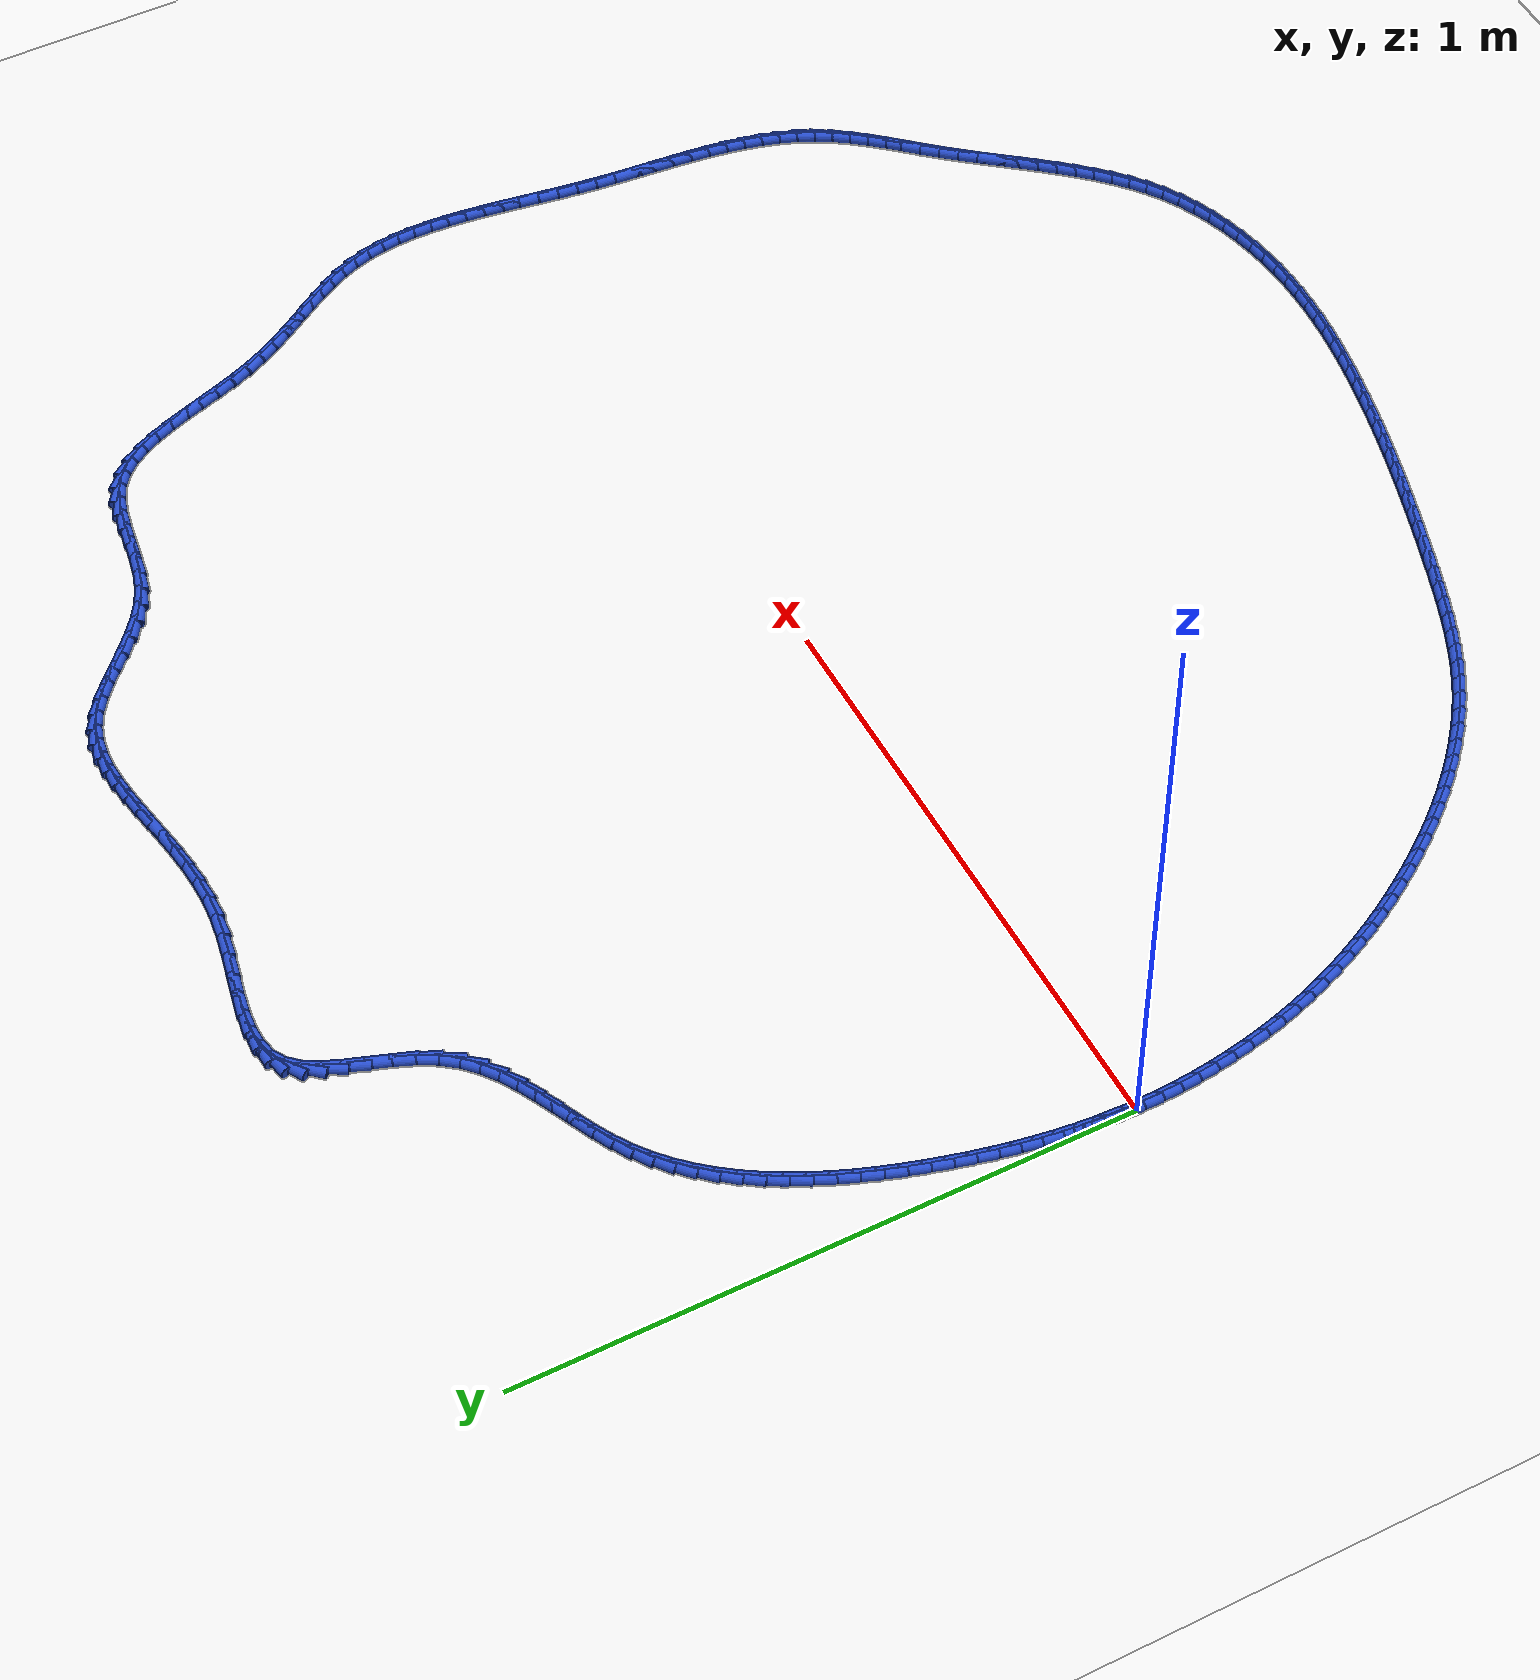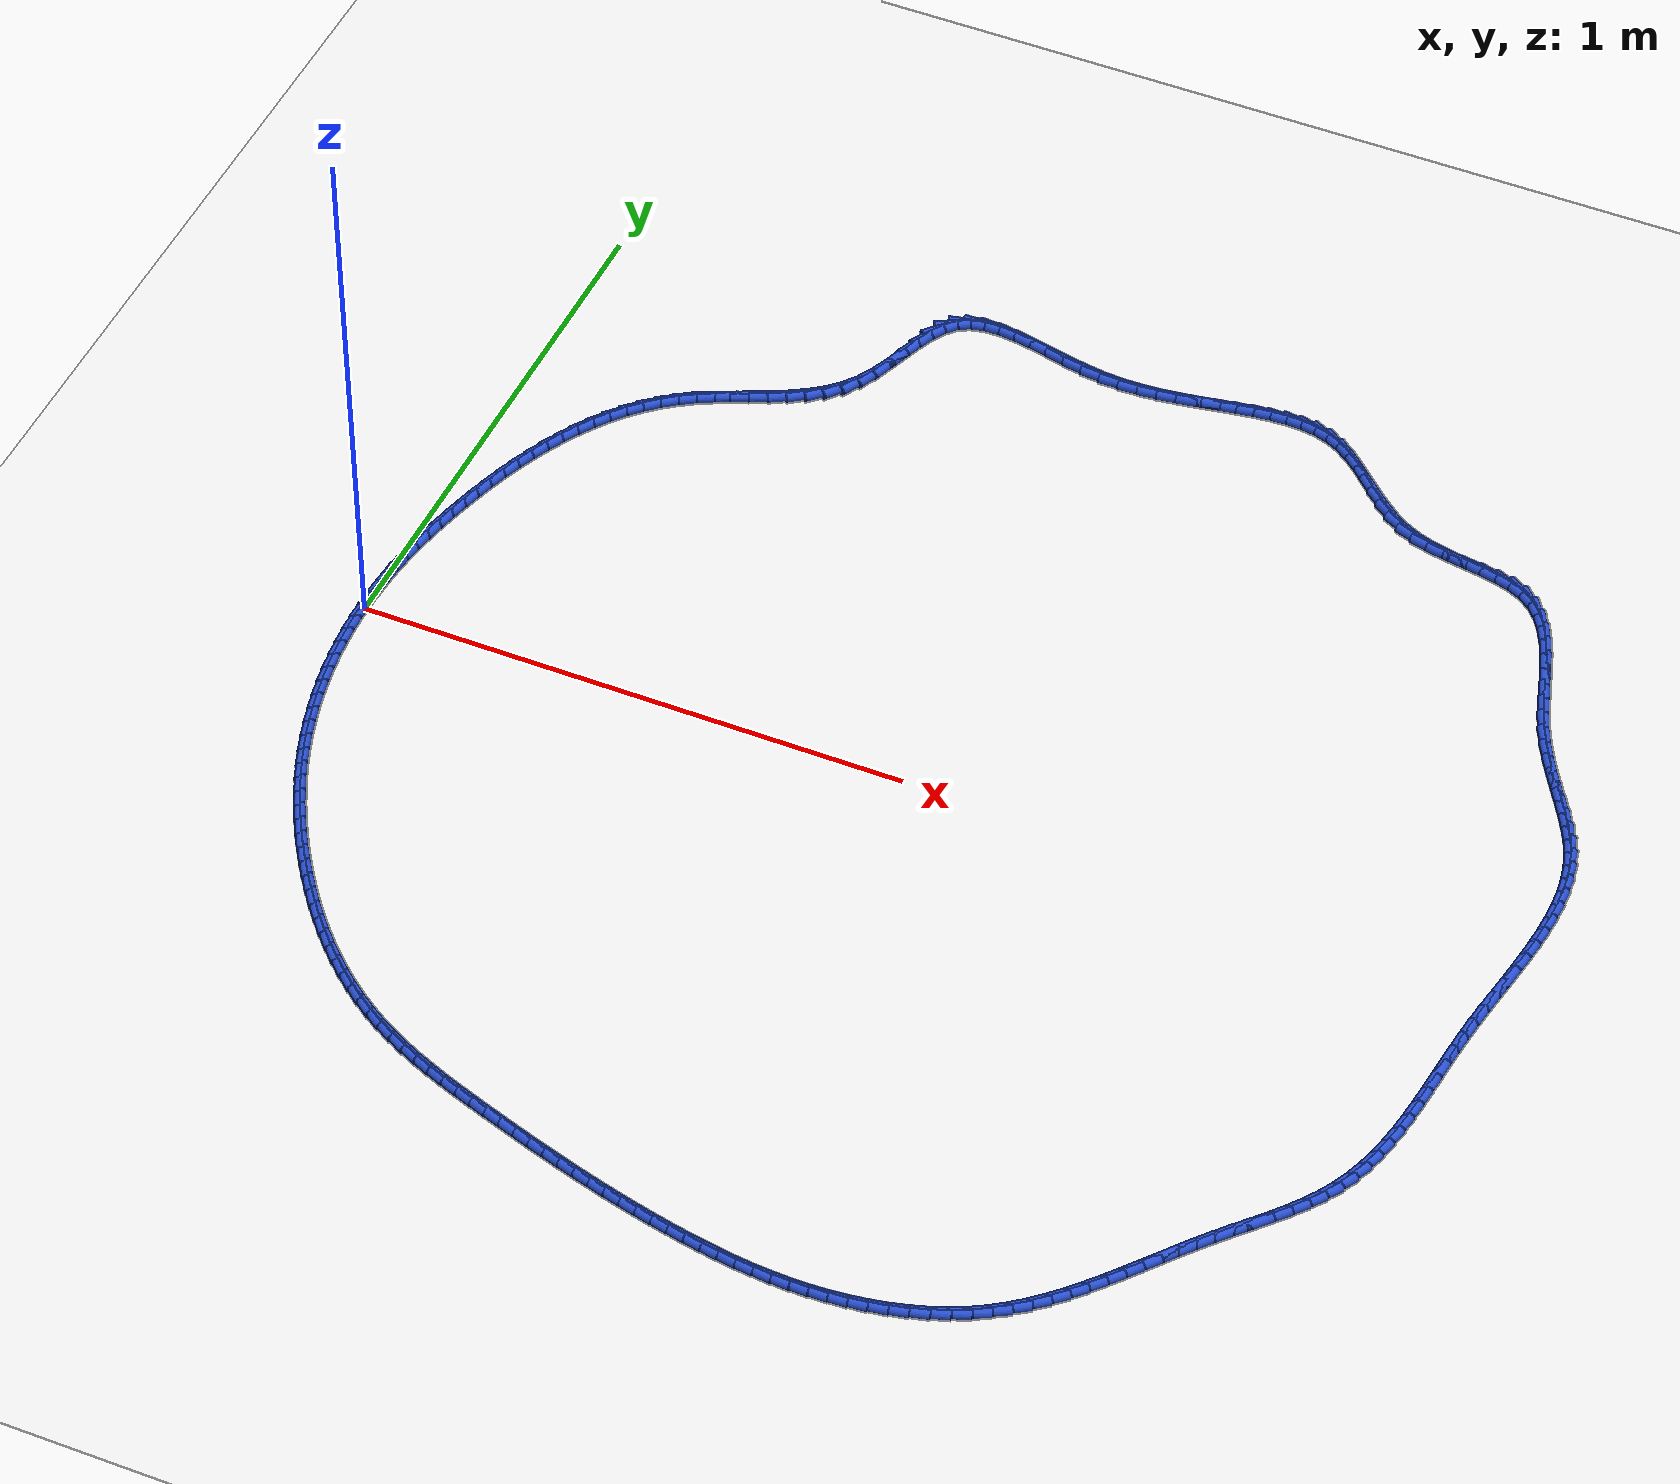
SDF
<sdf version="1.6">
 <world name="default">
  <light name="sun" type="directional">
   <pose>0 0 10 0 -0 0</pose>
   <diffuse>0.8 0.8 0.8 1</diffuse>
   <specular>0.2 0.2 0.2 1</specular>
   <attenuation>
    <range>1000</range>
    <constant>0.9</constant>
    <linear>0.01</linear>
    <quadratic>0.001</quadratic>
   </attenuation>
   <direction>-0.5 0.1 -0.9</direction>
  </light>
  <model name="ground_plane">
   <static>1</static>
   <link name="link">
    <collision name="collision">
     <geometry><plane><normal>0 0 1</normal><size>100 100</size></plane></geometry>
     <surface><friction><ode><mu>100</mu><mu2>50</mu2></ode></friction></surface>
    </collision>
    <visual name="visual">
     <cast_shadows>0</cast_shadows>
     <geometry><plane><normal>0 0 1</normal><size>100 100</size></plane></geometry>
     <material>
      <script><uri>file://media/materials/scripts/gazebo.material</uri><name>Gazebo/WhiteGlow</name></script>
     </material>
    </visual>
   </link>
  </model>
  <gravity>0 0 -9.8</gravity>
  <magnetic_field>6e-06 2.3e-05 -4.2e-05</magnetic_field>
  <atmosphere type="adiabatic"/>
  <physics name="default_physics" default="0" type="ode">
   <max_step_size>0.001</max_step_size>
   <real_time_factor>1</real_time_factor>
   <real_time_update_rate>1000</real_time_update_rate>
  </physics>
  <scene><ambient>0.4 0.4 0.4 1</ambient><background>0.7 0.7 0.7 1</background><shadows>1</shadows></scene>
  <spherical_coordinates>
   <surface_model>EARTH_WGS84</surface_model>
   <latitude_deg>0</latitude_deg>
   <longitude_deg>0</longitude_deg>
   <elevation>0</elevation>
   <heading_deg>0</heading_deg>
  </spherical_coordinates>
  <model name="line">
   <link name="link_0">
    <pose>-3.8163916471489756e-17 -5.551115123125783e-17 0.01 0 1.57 1.5481134711227669</pose>
    <collision name="collision">
     <geometry><cylinder><radius>0.01</radius><length>0.08</length></cylinder></geometry>
    </collision>
    <visual name="visual">
     <material>
      <script><name>Gazebo/Blue</name><uri>file://media/materials/scripts/gazebo.material</uri></script>
     </material>
     <geometry><cylinder><radius>0.01</radius><length>0.08</length></cylinder></geometry>
    </visual>
   </link>
   <link name="link_1">
    <pose>0.0007205756367423411 0.03176196424855339 0.01 0 1.57 1.5146938980342213</pose>
    <collision name="collision">
     <geometry><cylinder><radius>0.01</radius><length>0.08</length></cylinder></geometry>
    </collision>
    <visual name="visual">
     <material>
      <script><name>Gazebo/Blue</name><uri>file://media/materials/scripts/gazebo.material</uri></script>
     </material>
     <geometry><cylinder><radius>0.01</radius><length>0.08</length></cylinder></geometry>
    </visual>
   </link>
   <link name="link_2">
    <pose>0.0024987523179921083 0.06342388576557081 0.01 0 1.57 1.4823655658957862</pose>
    <collision name="collision">
     <geometry><cylinder><radius>0.01</radius><length>0.08</length></cylinder></geometry>
    </collision>
    <visual name="visual">
     <material>
      <script><name>Gazebo/Blue</name><uri>file://media/materials/scripts/gazebo.material</uri></script>
     </material>
     <geometry><cylinder><radius>0.01</radius><length>0.08</length></cylinder></geometry>
    </visual>
   </link>
   <link name="link_3">
    <pose>0.005299455204483686 0.09501242521603667 0.01 0 1.57 1.4512693870335382</pose>
    <collision name="collision">
     <geometry><cylinder><radius>0.01</radius><length>0.08</length></cylinder></geometry>
    </collision>
    <visual name="visual">
     <material>
      <script><name>Gazebo/Blue</name><uri>file://media/materials/scripts/gazebo.material</uri></script>
     </material>
     <geometry><cylinder><radius>0.01</radius><length>0.08</length></cylinder></geometry>
    </visual>
   </link>
   <link name="link_4">
    <pose>0.0090876094569515 0.12655424326493545 0.01 0 1.57 1.4215257989167212</pose>
    <collision name="collision">
     <geometry><cylinder><radius>0.01</radius><length>0.08</length></cylinder></geometry>
    </collision>
    <visual name="visual">
     <material>
      <script><name>Gazebo/Blue</name><uri>file://media/materials/scripts/gazebo.material</uri></script>
     </material>
     <geometry><cylinder><radius>0.01</radius><length>0.08</length></cylinder></geometry>
    </visual>
   </link>
   <link name="link_5">
    <pose>0.013828140236129967 0.15807600057725166 0.01 0 1.57 1.3932340660051605</pose>
    <collision name="collision">
     <geometry><cylinder><radius>0.01</radius><length>0.08</length></cylinder></geometry>
    </collision>
    <visual name="visual">
     <material>
      <script><name>Gazebo/Blue</name><uri>file://media/materials/scripts/gazebo.material</uri></script>
     </material>
     <geometry><cylinder><radius>0.01</radius><length>0.08</length></cylinder></geometry>
    </visual>
   </link>
   <link name="link_6">
    <pose>0.019485972702753523 0.1896043578179698 0.01 0 1.57 1.3664724228733238</pose>
    <collision name="collision">
     <geometry><cylinder><radius>0.01</radius><length>0.08</length></cylinder></geometry>
    </collision>
    <visual name="visual">
     <material>
      <script><name>Gazebo/Blue</name><uri>file://media/materials/scripts/gazebo.material</uri></script>
     </material>
     <geometry><cylinder><radius>0.01</radius><length>0.08</length></cylinder></geometry>
    </visual>
   </link>
   <link name="link_7">
    <pose>0.026026032017556586 0.22116597565207435 0.01 0 1.57 1.3412989221408662</pose>
    <collision name="collision">
     <geometry><cylinder><radius>0.01</radius><length>0.08</length></cylinder></geometry>
    </collision>
    <visual name="visual">
     <material>
      <script><name>Gazebo/Blue</name><uri>file://media/materials/scripts/gazebo.material</uri></script>
     </material>
     <geometry><cylinder><radius>0.01</radius><length>0.08</length></cylinder></geometry>
    </visual>
   </link>
   <link name="link_8">
    <pose>0.033413243341273574 0.25278751474454975 0.01 0 1.57 1.3177528258443836</pose>
    <collision name="collision">
     <geometry><cylinder><radius>0.01</radius><length>0.08</length></cylinder></geometry>
    </collision>
    <visual name="visual">
     <material>
      <script><name>Gazebo/Blue</name><uri>file://media/materials/scripts/gazebo.material</uri></script>
     </material>
     <geometry><cylinder><radius>0.01</radius><length>0.08</length></cylinder></geometry>
    </visual>
   </link>
   <link name="link_9">
    <pose>0.04161253183463892 0.28449563576038056 0.01 0 1.57 1.2956110362407625</pose>
    <collision name="collision">
     <geometry><cylinder><radius>0.01</radius><length>0.08</length></cylinder></geometry>
    </collision>
    <visual name="visual">
     <material>
      <script><name>Gazebo/Blue</name><uri>file://media/materials/scripts/gazebo.material</uri></script>
     </material>
     <geometry><cylinder><radius>0.01</radius><length>0.08</length></cylinder></geometry>
    </visual>
   </link>
   <link name="link_10">
    <pose>0.05059449479467364 0.31630723613009476 0.01 0 1.57 1.2720928596357388</pose>
    <collision name="collision">
     <geometry><cylinder><radius>0.01</radius><length>0.08</length></cylinder></geometry>
    </collision>
    <visual name="visual">
     <material>
      <script><name>Gazebo/Blue</name><uri>file://media/materials/scripts/gazebo.material</uri></script>
     </material>
     <geometry><cylinder><radius>0.01</radius><length>0.08</length></cylinder></geometry>
    </visual>
   </link>
   <link name="link_11">
    <pose>0.06039321889146027 0.3481299314187334 0.01 0 1.57 1.2453058232664884</pose>
    <collision name="collision">
     <geometry><cylinder><radius>0.01</radius><length>0.08</length></cylinder></geometry>
    </collision>
    <visual name="visual">
     <material>
      <script><name>Gazebo/Blue</name><uri>file://media/materials/scripts/gazebo.material</uri></script>
     </material>
     <geometry><cylinder><radius>0.01</radius><length>0.08</length></cylinder></geometry>
    </visual>
   </link>
   <link name="link_12">
    <pose>0.07108261791682259 0.3798027842674231 0.01 0 1.57 1.2149860125835699</pose>
    <collision name="collision">
     <geometry><cylinder><radius>0.01</radius><length>0.08</length></cylinder></geometry>
    </collision>
    <visual name="visual">
     <material>
      <script><name>Gazebo/Blue</name><uri>file://media/materials/scripts/gazebo.material</uri></script>
     </material>
     <geometry><cylinder><radius>0.01</radius><length>0.08</length></cylinder></geometry>
    </visual>
   </link>
   <link name="link_13">
    <pose>0.08273722032045311 0.4111637993298617 0.01 0 1.57 1.1808515463506217</pose>
    <collision name="collision">
     <geometry><cylinder><radius>0.01</radius><length>0.08</length></cylinder></geometry>
    </collision>
    <visual name="visual">
     <material>
      <script><name>Gazebo/Blue</name><uri>file://media/materials/scripts/gazebo.material</uri></script>
     </material>
     <geometry><cylinder><radius>0.01</radius><length>0.08</length></cylinder></geometry>
    </visual>
   </link>
   <link name="link_14">
    <pose>0.09543155455204444 0.4420509812597479 0.01 0 1.57 1.1425815779828539</pose>
    <collision name="collision">
     <geometry><cylinder><radius>0.01</radius><length>0.08</length></cylinder></geometry>
    </collision>
    <visual name="visual">
     <material>
      <script><name>Gazebo/Blue</name><uri>file://media/materials/scripts/gazebo.material</uri></script>
     </material>
     <geometry><cylinder><radius>0.01</radius><length>0.08</length></cylinder></geometry>
    </visual>
   </link>
   <link name="link_15">
    <pose>0.10924014906128902 0.4723023347107795 0.01 0 1.57 1.0998253803422684</pose>
    <collision name="collision">
     <geometry><cylinder><radius>0.01</radius><length>0.08</length></cylinder></geometry>
    </collision>
    <visual name="visual">
     <material>
      <script><name>Gazebo/Blue</name><uri>file://media/materials/scripts/gazebo.material</uri></script>
     </material>
     <geometry><cylinder><radius>0.01</radius><length>0.08</length></cylinder></geometry>
    </visual>
   </link>
   <link name="link_16">
    <pose>0.12423753229787945 0.5017558643366548 0.01 0 1.57 1.0522170919462064</pose>
    <collision name="collision">
     <geometry><cylinder><radius>0.01</radius><length>0.08</length></cylinder></geometry>
    </collision>
    <visual name="visual">
     <material>
      <script><name>Gazebo/Blue</name><uri>file://media/materials/scripts/gazebo.material</uri></script>
     </material>
     <geometry><cylinder><radius>0.01</radius><length>0.08</length></cylinder></geometry>
    </visual>
   </link>
   <link name="link_17">
    <pose>0.1404982327115083 0.530249574791072 0.01 0 1.57 0.9993986890427601</pose>
    <collision name="collision">
     <geometry><cylinder><radius>0.01</radius><length>0.08</length></cylinder></geometry>
    </collision>
    <visual name="visual">
     <material>
      <script><name>Gazebo/Blue</name><uri>file://media/materials/scripts/gazebo.material</uri></script>
     </material>
     <geometry><cylinder><radius>0.01</radius><length>0.08</length></cylinder></geometry>
    </visual>
   </link>
   <link name="link_18">
    <pose>0.15809677875186806 0.5576214707277295 0.01 0 1.57 0.9410538460700894</pose>
    <collision name="collision">
     <geometry><cylinder><radius>0.01</radius><length>0.08</length></cylinder></geometry>
    </collision>
    <visual name="visual">
     <material>
      <script><name>Gazebo/Blue</name><uri>file://media/materials/scripts/gazebo.material</uri></script>
     </material>
     <geometry><cylinder><radius>0.01</radius><length>0.08</length></cylinder></geometry>
    </visual>
   </link>
   <link name="link_19">
    <pose>0.17710769886865133 0.5837095568003254 0.01 0 1.57 0.8769546947000266</pose>
    <collision name="collision">
     <geometry><cylinder><radius>0.01</radius><length>0.08</length></cylinder></geometry>
    </collision>
    <visual name="visual">
     <material>
      <script><name>Gazebo/Blue</name><uri>file://media/materials/scripts/gazebo.material</uri></script>
     </material>
     <geometry><cylinder><radius>0.01</radius><length>0.08</length></cylinder></geometry>
    </visual>
   </link>
   <link name="link_20">
    <pose>0.19760552151155053 0.6083518376625577 0.01 0 1.57 0.807021449003432</pose>
    <collision name="collision">
     <geometry><cylinder><radius>0.01</radius><length>0.08</length></cylinder></geometry>
    </collision>
    <visual name="visual">
     <material>
      <script><name>Gazebo/Blue</name><uri>file://media/materials/scripts/gazebo.material</uri></script>
     </material>
     <geometry><cylinder><radius>0.01</radius><length>0.08</length></cylinder></geometry>
    </visual>
   </link>
   <link name="link_21">
    <pose>0.21966477513025834 0.6313863179681249 0.01 0 1.57 0.7313908101211046</pose>
    <collision name="collision">
     <geometry><cylinder><radius>0.01</radius><length>0.08</length></cylinder></geometry>
    </collision>
    <visual name="visual">
     <material>
      <script><name>Gazebo/Blue</name><uri>file://media/materials/scripts/gazebo.material</uri></script>
     </material>
     <geometry><cylinder><radius>0.01</radius><length>0.08</length></cylinder></geometry>
    </visual>
   </link>
   <link name="link_22">
    <pose>0.24335998817446725 0.652651002370725 0.01 0 1.57 0.6504829493605193</pose>
    <collision name="collision">
     <geometry><cylinder><radius>0.01</radius><length>0.08</length></cylinder></geometry>
    </collision>
    <visual name="visual">
     <material>
      <script><name>Gazebo/Blue</name><uri>file://media/materials/scripts/gazebo.material</uri></script>
     </material>
     <geometry><cylinder><radius>0.01</radius><length>0.08</length></cylinder></geometry>
    </visual>
   </link>
   <link name="link_23">
    <pose>0.26876568909386966 0.671983895524056 0.01 0 1.57 0.565586735130034</pose>
    <collision name="collision">
     <geometry><cylinder><radius>0.01</radius><length>0.08</length></cylinder></geometry>
    </collision>
    <visual name="visual">
     <material>
      <script><name>Gazebo/Blue</name><uri>file://media/materials/scripts/gazebo.material</uri></script>
     </material>
     <geometry><cylinder><radius>0.01</radius><length>0.08</length></cylinder></geometry>
    </visual>
   </link>
   <link name="link_24">
    <pose>0.2959456627580904 0.6892366464001525 0.01 0 1.57 0.49257284039773913</pose>
    <collision name="collision">
     <geometry><cylinder><radius>0.01</radius><length>0.08</length></cylinder></geometry>
    </collision>
    <visual name="visual">
     <material>
      <script><name>Gazebo/Blue</name><uri>file://media/materials/scripts/gazebo.material</uri></script>
     </material>
     <geometry><cylinder><radius>0.01</radius><length>0.08</length></cylinder></geometry>
    </visual>
   </link>
   <link name="link_25">
    <pose>0.3246594657160109 0.7046472731355861 0.01 0 1.57 0.4474584122082323</pose>
    <collision name="collision">
     <geometry><cylinder><radius>0.01</radius><length>0.08</length></cylinder></geometry>
    </collision>
    <visual name="visual">
     <material>
      <script><name>Gazebo/Blue</name><uri>file://media/materials/scripts/gazebo.material</uri></script>
     </material>
     <geometry><cylinder><radius>0.01</radius><length>0.08</length></cylinder></geometry>
    </visual>
   </link>
   <link name="link_26">
    <pose>0.3543268352935273 0.7188853633833977 0.01 0 1.57 0.42969119533140737</pose>
    <collision name="collision">
     <geometry><cylinder><radius>0.01</radius><length>0.08</length></cylinder></geometry>
    </collision>
    <visual name="visual">
     <material>
      <script><name>Gazebo/Blue</name><uri>file://media/materials/scripts/gazebo.material</uri></script>
     </material>
     <geometry><cylinder><radius>0.01</radius><length>0.08</length></cylinder></geometry>
    </visual>
   </link>
   <link name="link_27">
    <pose>0.3843496197321301 0.7326432238866161 0.01 0 1.57 0.438626696507426</pose>
    <collision name="collision">
     <geometry><cylinder><radius>0.01</radius><length>0.08</length></cylinder></geometry>
    </collision>
    <visual name="visual">
     <material>
      <script><name>Gazebo/Blue</name><uri>file://media/materials/scripts/gazebo.material</uri></script>
     </material>
     <geometry><cylinder><radius>0.01</radius><length>0.08</length></cylinder></geometry>
    </visual>
   </link>
   <link name="link_28">
    <pose>0.4141296672733101 0.7466131613882702 0.01 0 1.57 0.4747736686174871</pose>
    <collision name="collision">
     <geometry><cylinder><radius>0.01</radius><length>0.08</length></cylinder></geometry>
    </collision>
    <visual name="visual">
     <material>
      <script><name>Gazebo/Blue</name><uri>file://media/materials/scripts/gazebo.material</uri></script>
     </material>
     <geometry><cylinder><radius>0.01</radius><length>0.08</length></cylinder></geometry>
    </visual>
   </link>
   <link name="link_29">
    <pose>0.4430688261585577 0.7614874826313882 0.01 0 1.57 0.5396421532841285</pose>
    <collision name="collision">
     <geometry><cylinder><radius>0.01</radius><length>0.08</length></cylinder></geometry>
    </collision>
    <visual name="visual">
     <material>
      <script><name>Gazebo/Blue</name><uri>file://media/materials/scripts/gazebo.material</uri></script>
     </material>
     <geometry><cylinder><radius>0.01</radius><length>0.08</length></cylinder></geometry>
    </visual>
   </link>
   <link name="link_30">
    <pose>0.47056894462936416 0.7779584943590002 0.01 0 1.57 0.6349720782764744</pose>
    <collision name="collision">
     <geometry><cylinder><radius>0.01</radius><length>0.08</length></cylinder></geometry>
    </collision>
    <visual name="visual">
     <material>
      <script><name>Gazebo/Blue</name><uri>file://media/materials/scripts/gazebo.material</uri></script>
     </material>
     <geometry><cylinder><radius>0.01</radius><length>0.08</length></cylinder></geometry>
    </visual>
   </link>
   <link name="link_31">
    <pose>0.4960318709272196 0.7967185033141339 0.01 0 1.57 0.7610301727500743</pose>
    <collision name="collision">
     <geometry><cylinder><radius>0.01</radius><length>0.08</length></cylinder></geometry>
    </collision>
    <visual name="visual">
     <material>
      <script><name>Gazebo/Blue</name><uri>file://media/materials/scripts/gazebo.material</uri></script>
     </material>
     <geometry><cylinder><radius>0.01</radius><length>0.08</length></cylinder></geometry>
    </visual>
   </link>
   <link name="link_32">
    <pose>0.5188594532936152 0.8184598162398186 0.01 0 1.57 0.9140103487601109</pose>
    <collision name="collision">
     <geometry><cylinder><radius>0.01</radius><length>0.08</length></cylinder></geometry>
    </collision>
    <visual name="visual">
     <material>
      <script><name>Gazebo/Blue</name><uri>file://media/materials/scripts/gazebo.material</uri></script>
     </material>
     <geometry><cylinder><radius>0.01</radius><length>0.08</length></cylinder></geometry>
    </visual>
   </link>
   <link name="link_33">
    <pose>0.5384535399700541 0.8438747398790668 0.01 0 1.57 1.070606124262095</pose>
    <collision name="collision">
     <geometry><cylinder><radius>0.01</radius><length>0.08</length></cylinder></geometry>
    </collision>
    <visual name="visual">
     <material>
      <script><name>Gazebo/Blue</name><uri>file://media/materials/scripts/gazebo.material</uri></script>
     </material>
     <geometry><cylinder><radius>0.01</radius><length>0.08</length></cylinder></geometry>
    </visual>
   </link>
   <link name="link_34">
    <pose>0.5545105027063535 0.87325353032112 0.01 0 1.57 1.1747089015676233</pose>
    <collision name="collision">
     <geometry><cylinder><radius>0.01</radius><length>0.08</length></cylinder></geometry>
    </collision>
    <visual name="visual">
     <material>
      <script><name>Gazebo/Blue</name><uri>file://media/materials/scripts/gazebo.material</uri></script>
     </material>
     <geometry><cylinder><radius>0.01</radius><length>0.08</length></cylinder></geometry>
    </visual>
   </link>
   <link name="link_35">
    <pose>0.5679035801349451 0.9052799162093753 0.01 0 1.57 1.2243813752909718</pose>
    <collision name="collision">
     <geometry><cylinder><radius>0.01</radius><length>0.08</length></cylinder></geometry>
    </collision>
    <visual name="visual">
     <material>
      <script><name>Gazebo/Blue</name><uri>file://media/materials/scripts/gazebo.material</uri></script>
     </material>
     <geometry><cylinder><radius>0.01</radius><length>0.08</length></cylinder></geometry>
    </visual>
   </link>
   <link name="link_36">
    <pose>0.5797999211407465 0.9382364126819364 0.01 0 1.57 1.225629661575844</pose>
    <collision name="collision">
     <geometry><cylinder><radius>0.01</radius><length>0.08</length></cylinder></geometry>
    </collision>
    <visual name="visual">
     <material>
      <script><name>Gazebo/Blue</name><uri>file://media/materials/scripts/gazebo.material</uri></script>
     </material>
     <geometry><cylinder><radius>0.01</radius><length>0.08</length></cylinder></geometry>
    </visual>
   </link>
   <link name="link_37">
    <pose>0.5913666746086756 0.9704055348769074 0.01 0 1.57 1.1747361366580582</pose>
    <collision name="collision">
     <geometry><cylinder><radius>0.01</radius><length>0.08</length></cylinder></geometry>
    </collision>
    <visual name="visual">
     <material>
      <script><name>Gazebo/Blue</name><uri>file://media/materials/scripts/gazebo.material</uri></script>
     </material>
     <geometry><cylinder><radius>0.01</radius><length>0.08</length></cylinder></geometry>
    </visual>
   </link>
   <link name="link_38">
    <pose>0.6037709894236507 1.000069797932393 0.01 0 1.57 1.0554872220027178</pose>
    <collision name="collision">
     <geometry><cylinder><radius>0.01</radius><length>0.08</length></cylinder></geometry>
    </collision>
    <visual name="visual">
     <material>
      <script><name>Gazebo/Blue</name><uri>file://media/materials/scripts/gazebo.material</uri></script>
     </material>
     <geometry><cylinder><radius>0.01</radius><length>0.08</length></cylinder></geometry>
    </visual>
   </link>
   <link name="link_39">
    <pose>0.6181800144705891 1.0255117169864971 0.01 0 1.57 0.8371616474907234</pose>
    <collision name="collision">
     <geometry><cylinder><radius>0.01</radius><length>0.08</length></cylinder></geometry>
    </collision>
    <visual name="visual">
     <material>
      <script><name>Gazebo/Blue</name><uri>file://media/materials/scripts/gazebo.material</uri></script>
     </material>
     <geometry><cylinder><radius>0.01</radius><length>0.08</length></cylinder></geometry>
    </visual>
   </link>
   <link name="link_40">
    <pose>0.6357608784219339 1.045013841929786 0.01 0 1.57 0.5207232235269181</pose>
    <collision name="collision">
     <geometry><cylinder><radius>0.01</radius><length>0.08</length></cylinder></geometry>
    </collision>
    <visual name="visual">
     <material>
      <script><name>Gazebo/Blue</name><uri>file://media/materials/scripts/gazebo.material</uri></script>
     </material>
     <geometry><cylinder><radius>0.01</radius><length>0.08</length></cylinder></geometry>
    </visual>
   </link>
   <link name="link_41">
    <pose>0.6573637998049255 1.0574036043592596 0.01 0 1.57 0.2334394201693988</pose>
    <collision name="collision">
     <geometry><cylinder><radius>0.01</radius><length>0.08</length></cylinder></geometry>
    </collision>
    <visual name="visual">
     <material>
      <script><name>Gazebo/Blue</name><uri>file://media/materials/scripts/gazebo.material</uri></script>
     </material>
     <geometry><cylinder><radius>0.01</radius><length>0.08</length></cylinder></geometry>
    </visual>
   </link>
   <link name="link_42">
    <pose>0.6827198645647155 1.0634326244164793 0.01 0 1.57 0.029523971644871052</pose>
    <collision name="collision">
     <geometry><cylinder><radius>0.01</radius><length>0.08</length></cylinder></geometry>
    </collision>
    <visual name="visual">
     <material>
      <script><name>Gazebo/Blue</name><uri>file://media/materials/scripts/gazebo.material</uri></script>
     </material>
     <geometry><cylinder><radius>0.01</radius><length>0.08</length></cylinder></geometry>
    </visual>
   </link>
   <link name="link_43">
    <pose>0.7113132421604051 1.0642770598550158 0.01 0 1.57 -0.100696288666881</pose>
    <collision name="collision">
     <geometry><cylinder><radius>0.01</radius><length>0.08</length></cylinder></geometry>
    </collision>
    <visual name="visual">
     <material>
      <script><name>Gazebo/Blue</name><uri>file://media/materials/scripts/gazebo.material</uri></script>
     </material>
     <geometry><cylinder><radius>0.01</radius><length>0.08</length></cylinder></geometry>
    </visual>
   </link>
   <link name="link_44">
    <pose>0.7426281020510953 1.0611130684284382 0.01 0 1.57 -0.17701109667015702</pose>
    <collision name="collision">
     <geometry><cylinder><radius>0.01</radius><length>0.08</length></cylinder></geometry>
    </collision>
    <visual name="visual">
     <material>
      <script><name>Gazebo/Blue</name><uri>file://media/materials/scripts/gazebo.material</uri></script>
     </material>
     <geometry><cylinder><radius>0.01</radius><length>0.08</length></cylinder></geometry>
    </visual>
   </link>
   <link name="link_45">
    <pose>0.7761486136958874 1.0551168078903184 0.01 0 1.57 -0.2140051350356768</pose>
    <collision name="collision">
     <geometry><cylinder><radius>0.01</radius><length>0.08</length></cylinder></geometry>
    </collision>
    <visual name="visual">
     <material>
      <script><name>Gazebo/Blue</name><uri>file://media/materials/scripts/gazebo.material</uri></script>
     </material>
     <geometry><cylinder><radius>0.01</radius><length>0.08</length></cylinder></geometry>
    </visual>
   </link>
   <link name="link_46">
    <pose>0.8113589465538831 1.0474644359942253 0.01 0 1.57 -0.21989749776022657</pose>
    <collision name="collision">
     <geometry><cylinder><radius>0.01</radius><length>0.08</length></cylinder></geometry>
    </collision>
    <visual name="visual">
     <material>
      <script><name>Gazebo/Blue</name><uri>file://media/materials/scripts/gazebo.material</uri></script>
     </material>
     <geometry><cylinder><radius>0.01</radius><length>0.08</length></cylinder></geometry>
    </visual>
   </link>
   <link name="link_47">
    <pose>0.8477432700841827 1.0393321104937296 0.01 0 1.57 -0.1981125290597783</pose>
    <collision name="collision">
     <geometry><cylinder><radius>0.01</radius><length>0.08</length></cylinder></geometry>
    </collision>
    <visual name="visual">
     <material>
      <script><name>Gazebo/Blue</name><uri>file://media/materials/scripts/gazebo.material</uri></script>
     </material>
     <geometry><cylinder><radius>0.01</radius><length>0.08</length></cylinder></geometry>
    </visual>
   </link>
   <link name="link_48">
    <pose>0.8847857537458882 1.0318959891424015 0.01 0 1.57 -0.14852269965192388</pose>
    <collision name="collision">
     <geometry><cylinder><radius>0.01</radius><length>0.08</length></cylinder></geometry>
    </collision>
    <visual name="visual">
     <material>
      <script><name>Gazebo/Blue</name><uri>file://media/materials/scripts/gazebo.material</uri></script>
     </material>
     <geometry><cylinder><radius>0.01</radius><length>0.08</length></cylinder></geometry>
    </visual>
   </link>
   <link name="link_49">
    <pose>0.9219705669981006 1.026332229693811 0.01 0 1.57 -0.07107353629148604</pose>
    <collision name="collision">
     <geometry><cylinder><radius>0.01</radius><length>0.08</length></cylinder></geometry>
    </collision>
    <visual name="visual">
     <material>
      <script><name>Gazebo/Blue</name><uri>file://media/materials/scripts/gazebo.material</uri></script>
     </material>
     <geometry><cylinder><radius>0.01</radius><length>0.08</length></cylinder></geometry>
    </visual>
   </link>
   <link name="link_50">
    <pose>0.9588096042888374 1.0237095314111273 0.01 0 1.57 0.008771366517076952</pose>
    <collision name="collision">
     <geometry><cylinder><radius>0.01</radius><length>0.08</length></cylinder></geometry>
    </collision>
    <visual name="visual">
     <material>
      <script><name>Gazebo/Blue</name><uri>file://media/materials/scripts/gazebo.material</uri></script>
     </material>
     <geometry><cylinder><radius>0.01</radius><length>0.08</length></cylinder></geometry>
    </visual>
   </link>
   <link name="link_51">
    <pose>0.995090522766423 1.0240277728062113 0.01 0 1.57 0.07406109340477224</pose>
    <collision name="collision">
     <geometry><cylinder><radius>0.01</radius><length>0.08</length></cylinder></geometry>
    </collision>
    <visual name="visual">
     <material>
      <script><name>Gazebo/Blue</name><uri>file://media/materials/scripts/gazebo.material</uri></script>
     </material>
     <geometry><cylinder><radius>0.01</radius><length>0.08</length></cylinder></geometry>
    </visual>
   </link>
   <link name="link_52">
    <pose>1.0307590268013678 1.0266742616894737 0.01 0 1.57 0.12377375846647067</pose>
    <collision name="collision">
     <geometry><cylinder><radius>0.01</radius><length>0.08</length></cylinder></geometry>
    </collision>
    <visual name="visual">
     <material>
      <script><name>Gazebo/Blue</name><uri>file://media/materials/scripts/gazebo.material</uri></script>
     </material>
     <geometry><cylinder><radius>0.01</radius><length>0.08</length></cylinder></geometry>
    </visual>
   </link>
   <link name="link_53">
    <pose>1.0657626907885347 1.0310290578975063 0.01 0 1.57 0.1574418488207378</pose>
    <collision name="collision">
     <geometry><cylinder><radius>0.01</radius><length>0.08</length></cylinder></geometry>
    </collision>
    <visual name="visual">
     <material>
      <script><name>Gazebo/Blue</name><uri>file://media/materials/scripts/gazebo.material</uri></script>
     </material>
     <geometry><cylinder><radius>0.01</radius><length>0.08</length></cylinder></geometry>
    </visual>
   </link>
   <link name="link_54">
    <pose>1.1000490891227852 1.0364722212669004 0.01 0 1.57 0.17458184447944788</pose>
    <collision name="collision">
     <geometry><cylinder><radius>0.01</radius><length>0.08</length></cylinder></geometry>
    </collision>
    <visual name="visual">
     <material>
      <script><name>Gazebo/Blue</name><uri>file://media/materials/scripts/gazebo.material</uri></script>
     </material>
     <geometry><cylinder><radius>0.01</radius><length>0.08</length></cylinder></geometry>
    </visual>
   </link>
   <link name="link_55">
    <pose>1.1335657961989816 1.042383811634247 0.01 0 1.57 0.17438872050696594</pose>
    <collision name="collision">
     <geometry><cylinder><radius>0.01</radius><length>0.08</length></cylinder></geometry>
    </collision>
    <visual name="visual">
     <material>
      <script><name>Gazebo/Blue</name><uri>file://media/materials/scripts/gazebo.material</uri></script>
     </material>
     <geometry><cylinder><radius>0.01</radius><length>0.08</length></cylinder></geometry>
    </visual>
   </link>
   <link name="link_56">
    <pose>1.1662603864119871 1.0481438888361376 0.01 0 1.57 0.1555102897103206</pose>
    <collision name="collision">
     <geometry><cylinder><radius>0.01</radius><length>0.08</length></cylinder></geometry>
    </collision>
    <visual name="visual">
     <material>
      <script><name>Gazebo/Blue</name><uri>file://media/materials/scripts/gazebo.material</uri></script>
     </material>
     <geometry><cylinder><radius>0.01</radius><length>0.08</length></cylinder></geometry>
    </visual>
   </link>
   <link name="link_57">
    <pose>1.1980804341566633 1.0531325127091635 0.01 0 1.57 0.11591928147808699</pose>
    <collision name="collision">
     <geometry><cylinder><radius>0.01</radius><length>0.08</length></cylinder></geometry>
    </collision>
    <visual name="visual">
     <material>
      <script><name>Gazebo/Blue</name><uri>file://media/materials/scripts/gazebo.material</uri></script>
     </material>
     <geometry><cylinder><radius>0.01</radius><length>0.08</length></cylinder></geometry>
    </visual>
   </link>
   <link name="link_58">
    <pose>1.2289735138278726 1.056729743089917 0.01 0 1.57 0.05296617123826797</pose>
    <collision name="collision">
     <geometry><cylinder><radius>0.01</radius><length>0.08</length></cylinder></geometry>
    </collision>
    <visual name="visual">
     <material>
      <script><name>Gazebo/Blue</name><uri>file://media/materials/scripts/gazebo.material</uri></script>
     </material>
     <geometry><cylinder><radius>0.01</radius><length>0.08</length></cylinder></geometry>
    </visual>
   </link>
   <link name="link_59">
    <pose>1.2588871998204771 1.058315639814988 0.01 0 1.57 -0.036179134691694134</pose>
    <collision name="collision">
     <geometry><cylinder><radius>0.01</radius><length>0.08</length></cylinder></geometry>
    </collision>
    <visual name="visual">
     <material>
      <script><name>Gazebo/Blue</name><uri>file://media/materials/scripts/gazebo.material</uri></script>
     </material>
     <geometry><cylinder><radius>0.01</radius><length>0.08</length></cylinder></geometry>
    </visual>
   </link>
   <link name="link_60">
    <pose>1.2877690665293402 1.057270262720969 0.01 0 1.57 -0.15335329292305747</pose>
    <collision name="collision">
     <geometry><cylinder><radius>0.01</radius><length>0.08</length></cylinder></geometry>
    </collision>
    <visual name="visual">
     <material>
      <script><name>Gazebo/Blue</name><uri>file://media/materials/scripts/gazebo.material</uri></script>
     </material>
     <geometry><cylinder><radius>0.01</radius><length>0.08</length></cylinder></geometry>
    </visual>
   </link>
   <link name="link_61">
    <pose>1.3155666883493224 1.0529736716444504 0.01 0 1.57 -0.29727783499345267</pose>
    <collision name="collision">
     <geometry><cylinder><radius>0.01</radius><length>0.08</length></cylinder></geometry>
    </collision>
    <visual name="visual">
     <material>
      <script><name>Gazebo/Blue</name><uri>file://media/materials/scripts/gazebo.material</uri></script>
     </material>
     <geometry><cylinder><radius>0.01</radius><length>0.08</length></cylinder></geometry>
    </visual>
   </link>
   <link name="link_62">
    <pose>1.3422276396752877 1.0448059264220246 0.01 0 1.57 -0.4601765413912949</pose>
    <collision name="collision">
     <geometry><cylinder><radius>0.01</radius><length>0.08</length></cylinder></geometry>
    </collision>
    <visual name="visual">
     <material>
      <script><name>Gazebo/Blue</name><uri>file://media/materials/scripts/gazebo.material</uri></script>
     </material>
     <geometry><cylinder><radius>0.01</radius><length>0.08</length></cylinder></geometry>
    </visual>
   </link>
   <link name="link_63">
    <pose>1.3677074951348573 1.0321763604750855 0.01 0 1.57 -0.6034465025718819</pose>
    <collision name="collision">
     <geometry><cylinder><radius>0.01</radius><length>0.08</length></cylinder></geometry>
    </collision>
    <visual name="visual">
     <material>
      <script><name>Gazebo/Blue</name><uri>file://media/materials/scripts/gazebo.material</uri></script>
     </material>
     <geometry><cylinder><radius>0.01</radius><length>0.08</length></cylinder></geometry>
    </visual>
   </link>
   <link name="link_64">
    <pose>1.392183930482686 1.0153069956020342 0.01 0 1.57 -0.6965867125941612</pose>
    <collision name="collision">
     <geometry><cylinder><radius>0.01</radius><length>0.08</length></cylinder></geometry>
    </collision>
    <visual name="visual">
     <material>
      <script><name>Gazebo/Blue</name><uri>file://media/materials/scripts/gazebo.material</uri></script>
     </material>
     <geometry><cylinder><radius>0.01</radius><length>0.08</length></cylinder></geometry>
    </visual>
   </link>
   <link name="link_65">
    <pose>1.416080206524041 0.9953184718067046 0.01 0 1.57 -0.7457722344801025</pose>
    <collision name="collision">
     <geometry><cylinder><radius>0.01</radius><length>0.08</length></cylinder></geometry>
    </collision>
    <visual name="visual">
     <material>
      <script><name>Gazebo/Blue</name><uri>file://media/materials/scripts/gazebo.material</uri></script>
     </material>
     <geometry><cylinder><radius>0.01</radius><length>0.08</length></cylinder></geometry>
    </visual>
   </link>
   <link name="link_66">
    <pose>1.439832295960853 0.9733779430877325 0.01 0 1.57 -0.7572141190885201</pose>
    <collision name="collision">
     <geometry><cylinder><radius>0.01</radius><length>0.08</length></cylinder></geometry>
    </collision>
    <visual name="visual">
     <material>
      <script><name>Gazebo/Blue</name><uri>file://media/materials/scripts/gazebo.material</uri></script>
     </material>
     <geometry><cylinder><radius>0.01</radius><length>0.08</length></cylinder></geometry>
    </visual>
   </link>
   <link name="link_67">
    <pose>1.463876171495053 0.9506525634437559 0.01 0 1.57 -0.7338981056736787</pose>
    <collision name="collision">
     <geometry><cylinder><radius>0.01</radius><length>0.08</length></cylinder></geometry>
    </collision>
    <visual name="visual">
     <material>
      <script><name>Gazebo/Blue</name><uri>file://media/materials/scripts/gazebo.material</uri></script>
     </material>
     <geometry><cylinder><radius>0.01</radius><length>0.08</length></cylinder></geometry>
    </visual>
   </link>
   <link name="link_68">
    <pose>1.4886478058285726 0.928309486873411 0.01 0 1.57 -0.6758056952132081</pose>
    <collision name="collision">
     <geometry><cylinder><radius>0.01</radius><length>0.08</length></cylinder></geometry>
    </collision>
    <visual name="visual">
     <material>
      <script><name>Gazebo/Blue</name><uri>file://media/materials/scripts/gazebo.material</uri></script>
     </material>
     <geometry><cylinder><radius>0.01</radius><length>0.08</length></cylinder></geometry>
    </visual>
   </link>
   <link name="link_69">
    <pose>1.5145831716633429 0.9075158673753343 0.01 0 1.57 -0.580937040287492</pose>
    <collision name="collision">
     <geometry><cylinder><radius>0.01</radius><length>0.08</length></cylinder></geometry>
    </collision>
    <visual name="visual">
     <material>
      <script><name>Gazebo/Blue</name><uri>file://media/materials/scripts/gazebo.material</uri></script>
     </material>
     <geometry><cylinder><radius>0.01</radius><length>0.08</length></cylinder></geometry>
    </visual>
   </link>
   <link name="link_70">
    <pose>1.5421182417012942 0.8894388589481631 0.01 0 1.57 -0.44809035127467833</pose>
    <collision name="collision">
     <geometry><cylinder><radius>0.01</radius><length>0.08</length></cylinder></geometry>
    </collision>
    <visual name="visual">
     <material>
      <script><name>Gazebo/Blue</name><uri>file://media/materials/scripts/gazebo.material</uri></script>
     </material>
     <geometry><cylinder><radius>0.01</radius><length>0.08</length></cylinder></geometry>
    </visual>
   </link>
   <link name="link_71">
    <pose>1.5716801184723497 0.8752284061619208 0.01 0 1.57 -0.31081601795616426</pose>
    <collision name="collision">
     <geometry><cylinder><radius>0.01</radius><length>0.08</length></cylinder></geometry>
    </collision>
    <visual name="visual">
     <material>
      <script><name>Gazebo/Blue</name><uri>file://media/materials/scripts/gazebo.material</uri></script>
     </material>
     <geometry><cylinder><radius>0.01</radius><length>0.08</length></cylinder></geometry>
    </visual>
   </link>
   <link name="link_72">
    <pose>1.6032137205505768 0.8650989463204088 0.01 0 1.57 -0.21742986659875418</pose>
    <collision name="collision">
     <geometry><cylinder><radius>0.01</radius><length>0.08</length></cylinder></geometry>
    </collision>
    <visual name="visual">
     <material>
      <script><name>Gazebo/Blue</name><uri>file://media/materials/scripts/gazebo.material</uri></script>
     </material>
     <geometry><cylinder><radius>0.01</radius><length>0.08</length></cylinder></geometry>
    </visual>
   </link>
   <link name="link_73">
    <pose>1.635944009600703 0.8578680952200413 0.01 0 1.57 -0.16847662399609248</pose>
    <collision name="collision">
     <geometry><cylinder><radius>0.01</radius><length>0.08</length></cylinder></geometry>
    </collision>
    <visual name="visual">
     <material>
      <script><name>Gazebo/Blue</name><uri>file://media/materials/scripts/gazebo.material</uri></script>
     </material>
     <geometry><cylinder><radius>0.01</radius><length>0.08</length></cylinder></geometry>
    </visual>
   </link>
   <link name="link_74">
    <pose>1.6690371138983886 0.8522393232936207 0.01 0 1.57 -0.16175304164483764</pose>
    <collision name="collision">
     <geometry><cylinder><radius>0.01</radius><length>0.08</length></cylinder></geometry>
    </collision>
    <visual name="visual">
     <material>
      <script><name>Gazebo/Blue</name><uri>file://media/materials/scripts/gazebo.material</uri></script>
     </material>
     <geometry><cylinder><radius>0.01</radius><length>0.08</length></cylinder></geometry>
    </visual>
   </link>
   <link name="link_75">
    <pose>1.7016591617192947 0.8469161009739502 0.01 0 1.57 -0.19895413496557662</pose>
    <collision name="collision">
     <geometry><cylinder><radius>0.01</radius><length>0.08</length></cylinder></geometry>
    </collision>
    <visual name="visual">
     <material>
      <script><name>Gazebo/Blue</name><uri>file://media/materials/scripts/gazebo.material</uri></script>
     </material>
     <geometry><cylinder><radius>0.01</radius><length>0.08</length></cylinder></geometry>
    </visual>
   </link>
   <link name="link_76">
    <pose>1.7329762813390812 0.8406018986938322 0.01 0 1.57 -0.28667755892583996</pose>
    <collision name="collision">
     <geometry><cylinder><radius>0.01</radius><length>0.08</length></cylinder></geometry>
    </collision>
    <visual name="visual">
     <material>
      <script><name>Gazebo/Blue</name><uri>file://media/materials/scripts/gazebo.material</uri></script>
     </material>
     <geometry><cylinder><radius>0.01</radius><length>0.08</length></cylinder></geometry>
    </visual>
   </link>
   <link name="link_77">
    <pose>1.7621546010334086 0.8320001868860695 0.01 0 1.57 -0.43526158104750323</pose>
    <collision name="collision">
     <geometry><cylinder><radius>0.01</radius><length>0.08</length></cylinder></geometry>
    </collision>
    <visual name="visual">
     <material>
      <script><name>Gazebo/Blue</name><uri>file://media/materials/scripts/gazebo.material</uri></script>
     </material>
     <geometry><cylinder><radius>0.01</radius><length>0.08</length></cylinder></geometry>
    </visual>
   </link>
   <link name="link_78">
    <pose>1.7883602490779378 0.8198144359834652 0.01 0 1.57 -0.6373173418494269</pose>
    <collision name="collision">
     <geometry><cylinder><radius>0.01</radius><length>0.08</length></cylinder></geometry>
    </collision>
    <visual name="visual">
     <material>
      <script><name>Gazebo/Blue</name><uri>file://media/materials/scripts/gazebo.material</uri></script>
     </material>
     <geometry><cylinder><radius>0.01</radius><length>0.08</length></cylinder></geometry>
    </visual>
   </link>
   <link name="link_79">
    <pose>1.8109855847463407 0.8030630368696812 0.01 0 1.57 -0.8263623081606352</pose>
    <collision name="collision">
     <geometry><cylinder><radius>0.01</radius><length>0.08</length></cylinder></geometry>
    </collision>
    <visual name="visual">
     <material>
      <script><name>Gazebo/Blue</name><uri>file://media/materials/scripts/gazebo.material</uri></script>
     </material>
     <geometry><cylinder><radius>0.01</radius><length>0.08</length></cylinder></geometry>
    </visual>
   </link>
   <link name="link_80">
    <pose>1.8303453821268945 0.7820484099904159 0.01 0 1.57 -0.9768643043244373</pose>
    <collision name="collision">
     <geometry><cylinder><radius>0.01</radius><length>0.08</length></cylinder></geometry>
    </collision>
    <visual name="visual">
     <material>
      <script><name>Gazebo/Blue</name><uri>file://media/materials/scripts/gazebo.material</uri></script>
     </material>
     <geometry><cylinder><radius>0.01</radius><length>0.08</length></cylinder></geometry>
    </visual>
   </link>
   <link name="link_81">
    <pose>1.846989475903977 0.7574001873121311 0.01 0 1.57 -1.0884605117239807</pose>
    <collision name="collision">
     <geometry><cylinder><radius>0.01</radius><length>0.08</length></cylinder></geometry>
    </collision>
    <visual name="visual">
     <material>
      <script><name>Gazebo/Blue</name><uri>file://media/materials/scripts/gazebo.material</uri></script>
     </material>
     <geometry><cylinder><radius>0.01</radius><length>0.08</length></cylinder></geometry>
    </visual>
   </link>
   <link name="link_82">
    <pose>1.8614677008218918 0.7297480008847058 0.01 0 1.57 -1.1660822884992637</pose>
    <collision name="collision">
     <geometry><cylinder><radius>0.01</radius><length>0.08</length></cylinder></geometry>
    </collision>
    <visual name="visual">
     <material>
      <script><name>Gazebo/Blue</name><uri>file://media/materials/scripts/gazebo.material</uri></script>
     </material>
     <geometry><cylinder><radius>0.01</radius><length>0.08</length></cylinder></geometry>
    </visual>
   </link>
   <link name="link_83">
    <pose>1.87432989162494 0.6997214827580195 0.01 0 1.57 -1.2152917359677446</pose>
    <collision name="collision">
     <geometry><cylinder><radius>0.01</radius><length>0.08</length></cylinder></geometry>
    </collision>
    <visual name="visual">
     <material>
      <script><name>Gazebo/Blue</name><uri>file://media/materials/scripts/gazebo.material</uri></script>
     </material>
     <geometry><cylinder><radius>0.01</radius><length>0.08</length></cylinder></geometry>
    </visual>
   </link>
   <link name="link_84">
    <pose>1.8861258830574252 0.6679502649819506 0.01 0 1.57 -1.240381188543048</pose>
    <collision name="collision">
     <geometry><cylinder><radius>0.01</radius><length>0.08</length></cylinder></geometry>
    </collision>
    <visual name="visual">
     <material>
      <script><name>Gazebo/Blue</name><uri>file://media/materials/scripts/gazebo.material</uri></script>
     </material>
     <geometry><cylinder><radius>0.01</radius><length>0.08</length></cylinder></geometry>
    </visual>
   </link>
   <link name="link_85">
    <pose>1.89740550986365 0.6350639796063776 0.01 0 1.57 -1.2439522266429992</pose>
    <collision name="collision">
     <geometry><cylinder><radius>0.01</radius><length>0.08</length></cylinder></geometry>
    </collision>
    <visual name="visual">
     <material>
      <script><name>Gazebo/Blue</name><uri>file://media/materials/scripts/gazebo.material</uri></script>
     </material>
     <geometry><cylinder><radius>0.01</radius><length>0.08</length></cylinder></geometry>
    </visual>
   </link>
   <link name="link_86">
    <pose>1.9087186067879163 0.6016922586811804 0.01 0 1.57 -1.2269871215727104</pose>
    <collision name="collision">
     <geometry><cylinder><radius>0.01</radius><length>0.08</length></cylinder></geometry>
    </collision>
    <visual name="visual">
     <material>
      <script><name>Gazebo/Blue</name><uri>file://media/materials/scripts/gazebo.material</uri></script>
     </material>
     <geometry><cylinder><radius>0.01</radius><length>0.08</length></cylinder></geometry>
    </visual>
   </link>
   <link name="link_87">
    <pose>1.9206150085745262 0.5684647342562369 0.01 0 1.57 -1.18901390127267</pose>
    <collision name="collision">
     <geometry><cylinder><radius>0.01</radius><length>0.08</length></cylinder></geometry>
    </collision>
    <visual name="visual">
     <material>
      <script><name>Gazebo/Blue</name><uri>file://media/materials/scripts/gazebo.material</uri></script>
     </material>
     <geometry><cylinder><radius>0.01</radius><length>0.08</length></cylinder></geometry>
    </visual>
   </link>
   <link name="link_88">
    <pose>1.9336445499677832 0.5360110383814258 0.01 0 1.57 -1.1302857701732456</pose>
    <collision name="collision">
     <geometry><cylinder><radius>0.01</radius><length>0.08</length></cylinder></geometry>
    </collision>
    <visual name="visual">
     <material>
      <script><name>Gazebo/Blue</name><uri>file://media/materials/scripts/gazebo.material</uri></script>
     </material>
     <geometry><cylinder><radius>0.01</radius><length>0.08</length></cylinder></geometry>
    </visual>
   </link>
   <link name="link_89">
    <pose>1.9483031106873607 0.5049155267428569 0.01 0 1.57 -1.0721602643925197</pose>
    <collision name="collision">
     <geometry><cylinder><radius>0.01</radius><length>0.08</length></cylinder></geometry>
    </collision>
    <visual name="visual">
     <material>
      <script><name>Gazebo/Blue</name><uri>file://media/materials/scripts/gazebo.material</uri></script>
     </material>
     <geometry><cylinder><radius>0.01</radius><length>0.08</length></cylinder></geometry>
    </visual>
   </link>
   <link name="link_90">
    <pose>1.9644628609901937 0.4752391691748766 0.01 0 1.57 -1.0300450297470933</pose>
    <collision name="collision">
     <geometry><cylinder><radius>0.01</radius><length>0.08</length></cylinder></geometry>
    </collision>
    <visual name="visual">
     <material>
      <script><name>Gazebo/Blue</name><uri>file://media/materials/scripts/gazebo.material</uri></script>
     </material>
     <geometry><cylinder><radius>0.01</radius><length>0.08</length></cylinder></geometry>
    </visual>
   </link>
   <link name="link_91">
    <pose>1.9815952419973895 0.4467066636214566 0.01 0 1.57 -1.0050455775173879</pose>
    <collision name="collision">
     <geometry><cylinder><radius>0.01</radius><length>0.08</length></cylinder></geometry>
    </collision>
    <visual name="visual">
     <material>
      <script><name>Gazebo/Blue</name><uri>file://media/materials/scripts/gazebo.material</uri></script>
     </material>
     <geometry><cylinder><radius>0.01</radius><length>0.08</length></cylinder></geometry>
    </visual>
   </link>
   <link name="link_92">
    <pose>1.9991650903770979 0.4190371658992756 0.01 0 1.57 -0.9979226503031484</pose>
    <collision name="collision">
     <geometry><cylinder><radius>0.01</radius><length>0.08</length></cylinder></geometry>
    </collision>
    <visual name="visual">
     <material>
      <script><name>Gazebo/Blue</name><uri>file://media/materials/scripts/gazebo.material</uri></script>
     </material>
     <geometry><cylinder><radius>0.01</radius><length>0.08</length></cylinder></geometry>
    </visual>
   </link>
   <link name="link_93">
    <pose>2.0166372427974713 0.391949831825013 0.01 0 1.57 -1.0095695049526292</pose>
    <collision name="collision">
     <geometry><cylinder><radius>0.01</radius><length>0.08</length></cylinder></geometry>
    </collision>
    <visual name="visual">
     <material>
      <script><name>Gazebo/Blue</name><uri>file://media/materials/scripts/gazebo.material</uri></script>
     </material>
     <geometry><cylinder><radius>0.01</radius><length>0.08</length></cylinder></geometry>
    </visual>
   </link>
   <link name="link_94">
    <pose>2.0334765359266576 0.36516381721534696 0.01 0 1.57 -1.041105508390965</pose>
    <collision name="collision">
     <geometry><cylinder><radius>0.01</radius><length>0.08</length></cylinder></geometry>
    </collision>
    <visual name="visual">
     <material>
      <script><name>Gazebo/Blue</name><uri>file://media/materials/scripts/gazebo.material</uri></script>
     </material>
     <geometry><cylinder><radius>0.01</radius><length>0.08</length></cylinder></geometry>
    </visual>
   </link>
   <link name="link_95">
    <pose>2.0491478064328095 0.3383982778869563 0.01 0 1.57 -1.0937672437504518</pose>
    <collision name="collision">
     <geometry><cylinder><radius>0.01</radius><length>0.08</length></cylinder></geometry>
    </collision>
    <visual name="visual">
     <material>
      <script><name>Gazebo/Blue</name><uri>file://media/materials/scripts/gazebo.material</uri></script>
     </material>
     <geometry><cylinder><radius>0.01</radius><length>0.08</length></cylinder></geometry>
    </visual>
   </link>
   <link name="link_96">
    <pose>2.0631158909840766 0.31137236965652026 0.01 0 1.57 -1.1685045502220708</pose>
    <collision name="collision">
     <geometry><cylinder><radius>0.01</radius><length>0.08</length></cylinder></geometry>
    </collision>
    <visual name="visual">
     <material>
      <script><name>Gazebo/Blue</name><uri>file://media/materials/scripts/gazebo.material</uri></script>
     </material>
     <geometry><cylinder><radius>0.01</radius><length>0.08</length></cylinder></geometry>
    </visual>
   </link>
   <link name="link_97">
    <pose>2.0748456262486097 0.2838052483407173 0.01 0 1.57 -1.2624765797729067</pose>
    <collision name="collision">
     <geometry><cylinder><radius>0.01</radius><length>0.08</length></cylinder></geometry>
    </collision>
    <visual name="visual">
     <material>
      <script><name>Gazebo/Blue</name><uri>file://media/materials/scripts/gazebo.material</uri></script>
     </material>
     <geometry><cylinder><radius>0.01</radius><length>0.08</length></cylinder></geometry>
    </visual>
   </link>
   <link name="link_98">
    <pose>2.083876671234208 0.2554481676941861 0.01 0 1.57 -1.355247311664079</pose>
    <collision name="collision">
     <geometry><cylinder><radius>0.01</radius><length>0.08</length></cylinder></geometry>
    </collision>
    <visual name="visual">
     <material>
      <script><name>Gazebo/Blue</name><uri>file://media/materials/scripts/gazebo.material</uri></script>
     </material>
     <geometry><cylinder><radius>0.01</radius><length>0.08</length></cylinder></geometry>
    </visual>
   </link>
   <link name="link_99">
    <pose>2.090264448434018 0.2262736381768829 0.01 0 1.57 -1.4373540266387814</pose>
    <collision name="collision">
     <geometry><cylinder><radius>0.01</radius><length>0.08</length></cylinder></geometry>
    </collision>
    <visual name="visual">
     <material>
      <script><name>Gazebo/Blue</name><uri>file://media/materials/scripts/gazebo.material</uri></script>
     </material>
     <geometry><cylinder><radius>0.01</radius><length>0.08</length></cylinder></geometry>
    </visual>
   </link>
   <link name="link_100">
    <pose>2.0942817456433493 0.19634741750641654 0.01 0 1.57 -1.5081455812263116</pose>
    <collision name="collision">
     <geometry><cylinder><radius>0.01</radius><length>0.08</length></cylinder></geometry>
    </collision>
    <visual name="visual">
     <material>
      <script><name>Gazebo/Blue</name><uri>file://media/materials/scripts/gazebo.material</uri></script>
     </material>
     <geometry><cylinder><radius>0.01</radius><length>0.08</length></cylinder></geometry>
    </visual>
   </link>
   <link name="link_101">
    <pose>2.096202112653878 0.1657355902882238 0.01 0 1.57 -1.567690912067675</pose>
    <collision name="collision">
     <geometry><cylinder><radius>0.01</radius><length>0.08</length></cylinder></geometry>
    </collision>
    <visual name="visual">
     <material>
      <script><name>Gazebo/Blue</name><uri>file://media/materials/scripts/gazebo.material</uri></script>
     </material>
     <geometry><cylinder><radius>0.01</radius><length>0.08</length></cylinder></geometry>
    </visual>
   </link>
   <link name="link_102">
    <pose>2.096299099257279 0.1345042411277429 0.01 0 1.57 1.5251193337158413</pose>
    <collision name="collision">
     <geometry><cylinder><radius>0.01</radius><length>0.08</length></cylinder></geometry>
    </collision>
    <visual name="visual">
     <material>
      <script><name>Gazebo/Blue</name><uri>file://media/materials/scripts/gazebo.material</uri></script>
     </material>
     <geometry><cylinder><radius>0.01</radius><length>0.08</length></cylinder></geometry>
    </visual>
   </link>
   <link name="link_103">
    <pose>2.0948462552452303 0.10271945463041103 0.01 0 1.57 1.4864310822576539</pose>
    <collision name="collision">
     <geometry><cylinder><radius>0.01</radius><length>0.08</length></cylinder></geometry>
    </collision>
    <visual name="visual">
     <material>
      <script><name>Gazebo/Blue</name><uri>file://media/materials/scripts/gazebo.material</uri></script>
     </material>
     <geometry><cylinder><radius>0.01</radius><length>0.08</length></cylinder></geometry>
    </visual>
   </link>
   <link name="link_104">
    <pose>2.0921171304094055 0.0704473154016655 0.01 0 1.57 1.4571412024107437</pose>
    <collision name="collision">
     <geometry><cylinder><radius>0.01</radius><length>0.08</length></cylinder></geometry>
    </collision>
    <visual name="visual">
     <material>
      <script><name>Gazebo/Blue</name><uri>file://media/materials/scripts/gazebo.material</uri></script>
     </material>
     <geometry><cylinder><radius>0.01</radius><length>0.08</length></cylinder></geometry>
    </visual>
   </link>
   <link name="link_105">
    <pose>2.0883852745414813 0.0377539080469439 0.01 0 1.57 1.436623130697134</pose>
    <collision name="collision">
     <geometry><cylinder><radius>0.01</radius><length>0.08</length></cylinder></geometry>
    </collision>
    <visual name="visual">
     <material>
      <script><name>Gazebo/Blue</name><uri>file://media/materials/scripts/gazebo.material</uri></script>
     </material>
     <geometry><cylinder><radius>0.01</radius><length>0.08</length></cylinder></geometry>
    </visual>
   </link>
   <link name="link_106">
    <pose>2.0839242374331355 0.004705317171682859 0.01 0 1.57 1.4243710680460435</pose>
    <collision name="collision">
     <geometry><cylinder><radius>0.01</radius><length>0.08</length></cylinder></geometry>
    </collision>
    <visual name="visual">
     <material>
      <script><name>Gazebo/Blue</name><uri>file://media/materials/scripts/gazebo.material</uri></script>
     </material>
     <geometry><cylinder><radius>0.01</radius><length>0.08</length></cylinder></geometry>
    </visual>
   </link>
   <link name="link_107">
    <pose>2.0790075688760417 -0.028632372618678688 0.01 0 1.57 1.420023100240832</pose>
    <collision name="collision">
     <geometry><cylinder><radius>0.01</radius><length>0.08</length></cylinder></geometry>
    </collision>
    <visual name="visual">
     <material>
      <script><name>Gazebo/Blue</name><uri>file://media/materials/scripts/gazebo.material</uri></script>
     </material>
     <geometry><cylinder><radius>0.01</radius><length>0.08</length></cylinder></geometry>
    </visual>
   </link>
   <link name="link_108">
    <pose>2.0739088186618773 -0.062193076718704 0.01 0 1.57 1.423367499479504</pose>
    <collision name="collision">
     <geometry><cylinder><radius>0.01</radius><length>0.08</length></cylinder></geometry>
    </collision>
    <visual name="visual">
     <material>
      <script><name>Gazebo/Blue</name><uri>file://media/materials/scripts/gazebo.material</uri></script>
     </material>
     <geometry><cylinder><radius>0.01</radius><length>0.08</length></cylinder></geometry>
    </visual>
   </link>
   <link name="link_109">
    <pose>2.0689015365823193 -0.0959107105229556 0.01 0 1.57 1.4343390073322952</pose>
    <collision name="collision">
     <geometry><cylinder><radius>0.01</radius><length>0.08</length></cylinder></geometry>
    </collision>
    <visual name="visual">
     <material>
      <script><name>Gazebo/Blue</name><uri>file://media/materials/scripts/gazebo.material</uri></script>
     </material>
     <geometry><cylinder><radius>0.01</radius><length>0.08</length></cylinder></geometry>
    </visual>
   </link>
   <link name="link_110">
    <pose>2.064259272429042 -0.12971918942599614 0.01 0 1.57 1.45286953223892</pose>
    <collision name="collision">
     <geometry><cylinder><radius>0.01</radius><length>0.08</length></cylinder></geometry>
    </collision>
    <visual name="visual">
     <material>
      <script><name>Gazebo/Blue</name><uri>file://media/materials/scripts/gazebo.material</uri></script>
     </material>
     <geometry><cylinder><radius>0.01</radius><length>0.08</length></cylinder></geometry>
    </visual>
   </link>
   <link name="link_111">
    <pose>2.0602508483165964 -0.16355225952494912 0.01 0 1.57 1.4728388241207218</pose>
    <collision name="collision">
     <geometry><cylinder><radius>0.01</radius><length>0.08</length></cylinder></geometry>
    </collision>
    <visual name="visual">
     <material>
      <script><name>Gazebo/Blue</name><uri>file://media/materials/scripts/gazebo.material</uri></script>
     </material>
     <geometry><cylinder><radius>0.01</radius><length>0.08</length></cylinder></geometry>
    </visual>
   </link>
   <link name="link_112">
    <pose>2.0569308519390166 -0.19733599521310893 0.01 0 1.57 1.4855852672893437</pose>
    <collision name="collision">
     <geometry><cylinder><radius>0.01</radius><length>0.08</length></cylinder></geometry>
    </collision>
    <visual name="visual">
     <material>
      <script><name>Gazebo/Blue</name><uri>file://media/materials/scripts/gazebo.material</uri></script>
     </material>
     <geometry><cylinder><radius>0.01</radius><length>0.08</length></cylinder></geometry>
    </visual>
   </link>
   <link name="link_113">
    <pose>2.0540565543185485 -0.2309858240164514 0.01 0 1.57 1.4904079318704284</pose>
    <collision name="collision">
     <geometry><cylinder><radius>0.01</radius><length>0.08</length></cylinder></geometry>
    </collision>
    <visual name="visual">
     <material>
      <script><name>Gazebo/Blue</name><uri>file://media/materials/scripts/gazebo.material</uri></script>
     </material>
     <geometry><cylinder><radius>0.01</radius><length>0.08</length></cylinder></geometry>
    </visual>
   </link>
   <link name="link_114">
    <pose>2.051363320866398 -0.2644163890241696 0.01 0 1.57 1.4871661916958354</pose>
    <collision name="collision">
     <geometry><cylinder><radius>0.01</radius><length>0.08</length></cylinder></geometry>
    </collision>
    <visual name="visual">
     <material>
      <script><name>Gazebo/Blue</name><uri>file://media/materials/scripts/gazebo.material</uri></script>
     </material>
     <geometry><cylinder><radius>0.01</radius><length>0.08</length></cylinder></geometry>
    </visual>
   </link>
   <link name="link_115">
    <pose>2.048586516993774 -0.29754233332545604 0.01 0 1.57 1.4756237007833684</pose>
    <collision name="collision">
     <geometry><cylinder><radius>0.01</radius><length>0.08</length></cylinder></geometry>
    </collision>
    <visual name="visual">
     <material>
      <script><name>Gazebo/Blue</name><uri>file://media/materials/scripts/gazebo.material</uri></script>
     </material>
     <geometry><cylinder><radius>0.01</radius><length>0.08</length></cylinder></geometry>
    </visual>
   </link>
   <link name="link_116">
    <pose>2.0454615081118837 -0.3302783000095029 0.01 0 1.57 1.4554465817064046</pose>
    <collision name="collision">
     <geometry><cylinder><radius>0.01</radius><length>0.08</length></cylinder></geometry>
    </collision>
    <visual name="visual">
     <material>
      <script><name>Gazebo/Blue</name><uri>file://media/materials/scripts/gazebo.material</uri></script>
     </material>
     <geometry><cylinder><radius>0.01</radius><length>0.08</length></cylinder></geometry>
    </visual>
   </link>
   <link name="link_117">
    <pose>2.0417236596319333 -0.3625389321655025 0.01 0 1.57 1.4262181396266804</pose>
    <collision name="collision">
     <geometry><cylinder><radius>0.01</radius><length>0.08</length></cylinder></geometry>
    </collision>
    <visual name="visual">
     <material>
      <script><name>Gazebo/Blue</name><uri>file://media/materials/scripts/gazebo.material</uri></script>
     </material>
     <geometry><cylinder><radius>0.01</radius><length>0.08</length></cylinder></geometry>
    </visual>
   </link>
   <link name="link_118">
    <pose>2.037108336965131 -0.39423887288264703 0.01 0 1.57 1.3874765862404939</pose>
    <collision name="collision">
     <geometry><cylinder><radius>0.01</radius><length>0.08</length></cylinder></geometry>
    </collision>
    <visual name="visual">
     <material>
      <script><name>Gazebo/Blue</name><uri>file://media/materials/scripts/gazebo.material</uri></script>
     </material>
     <geometry><cylinder><radius>0.01</radius><length>0.08</length></cylinder></geometry>
    </visual>
   </link>
   <link name="link_119">
    <pose>2.0313509055226846 -0.4252927652501298 0.01 0 1.57 1.3387848964010884</pose>
    <collision name="collision">
     <geometry><cylinder><radius>0.01</radius><length>0.08</length></cylinder></geometry>
    </collision>
    <visual name="visual">
     <material>
      <script><name>Gazebo/Blue</name><uri>file://media/materials/scripts/gazebo.material</uri></script>
     </material>
     <geometry><cylinder><radius>0.01</radius><length>0.08</length></cylinder></geometry>
    </visual>
   </link>
   <link name="link_120">
    <pose>2.0241867307158015 -0.4556152523571417 0.01 0 1.57 1.2798422230376436</pose>
    <collision name="collision">
     <geometry><cylinder><radius>0.01</radius><length>0.08</length></cylinder></geometry>
    </collision>
    <visual name="visual">
     <material>
      <script><name>Gazebo/Blue</name><uri>file://media/materials/scripts/gazebo.material</uri></script>
     </material>
     <geometry><cylinder><radius>0.01</radius><length>0.08</length></cylinder></geometry>
    </visual>
   </link>
   <link name="link_121">
    <pose>2.0153511779556883 -0.4851209772928755 0.01 0 1.57 1.2106405768051407</pose>
    <collision name="collision">
     <geometry><cylinder><radius>0.01</radius><length>0.08</length></cylinder></geometry>
    </collision>
    <visual name="visual">
     <material>
      <script><name>Gazebo/Blue</name><uri>file://media/materials/scripts/gazebo.material</uri></script>
     </material>
     <geometry><cylinder><radius>0.01</radius><length>0.08</length></cylinder></geometry>
    </visual>
   </link>
   <link name="link_122">
    <pose>2.0045796126535524 -0.5137245831465236 0.01 0 1.57 1.131654007607248</pose>
    <collision name="collision">
     <geometry><cylinder><radius>0.01</radius><length>0.08</length></cylinder></geometry>
    </collision>
    <visual name="visual">
     <material>
      <script><name>Gazebo/Blue</name><uri>file://media/materials/scripts/gazebo.material</uri></script>
     </material>
     <geometry><cylinder><radius>0.01</radius><length>0.08</length></cylinder></geometry>
    </visual>
   </link>
   <link name="link_123">
    <pose>1.9916074002206023 -0.5413407130072785 0.01 0 1.57 1.0451725270043952</pose>
    <collision name="collision">
     <geometry><cylinder><radius>0.01</radius><length>0.08</length></cylinder></geometry>
    </collision>
    <visual name="visual">
     <material>
      <script><name>Gazebo/Blue</name><uri>file://media/materials/scripts/gazebo.material</uri></script>
     </material>
     <geometry><cylinder><radius>0.01</radius><length>0.08</length></cylinder></geometry>
    </visual>
   </link>
   <link name="link_124">
    <pose>1.976202319411012 -0.5678987489880347 0.01 0 1.57 0.9674167000876301</pose>
    <collision name="collision">
     <geometry><cylinder><radius>0.01</radius><length>0.08</length></cylinder></geometry>
    </collision>
    <visual name="visual">
     <material>
      <script><name>Gazebo/Blue</name><uri>file://media/materials/scripts/gazebo.material</uri></script>
     </material>
     <geometry><cylinder><radius>0.01</radius><length>0.08</length></cylinder></geometry>
    </visual>
   </link>
   <link name="link_125">
    <pose>1.958548316613259 -0.5935173133128465 0.01 0 1.57 0.9087192559915132</pose>
    <collision name="collision">
     <geometry><cylinder><radius>0.01</radius><length>0.08</length></cylinder></geometry>
    </collision>
    <visual name="visual">
     <material>
      <script><name>Gazebo/Blue</name><uri>file://media/materials/scripts/gazebo.material</uri></script>
     </material>
     <geometry><cylinder><radius>0.01</radius><length>0.08</length></cylinder></geometry>
    </visual>
   </link>
   <link name="link_126">
    <pose>1.9391177890825895 -0.6184461928365337 0.01 0 1.57 0.8684158583701903</pose>
    <collision name="collision">
     <geometry><cylinder><radius>0.01</radius><length>0.08</length></cylinder></geometry>
    </collision>
    <visual name="visual">
     <material>
      <script><name>Gazebo/Blue</name><uri>file://media/materials/scripts/gazebo.material</uri></script>
     </material>
     <geometry><cylinder><radius>0.01</radius><length>0.08</length></cylinder></geometry>
    </visual>
   </link>
   <link name="link_127">
    <pose>1.9183889232389297 -0.6429378068679523 0.01 0 1.57 0.8454654493782684</pose>
    <collision name="collision">
     <geometry><cylinder><radius>0.01</radius><length>0.08</length></cylinder></geometry>
    </collision>
    <visual name="visual">
     <material>
      <script><name>Gazebo/Blue</name><uri>file://media/materials/scripts/gazebo.material</uri></script>
     </material>
     <geometry><cylinder><radius>0.01</radius><length>0.08</length></cylinder></geometry>
    </visual>
   </link>
   <link name="link_128">
    <pose>1.896839905502205 -0.6672445747159574 0.01 0 1.57 0.8390231392994352</pose>
    <collision name="collision">
     <geometry><cylinder><radius>0.01</radius><length>0.08</length></cylinder></geometry>
    </collision>
    <visual name="visual">
     <material>
      <script><name>Gazebo/Blue</name><uri>file://media/materials/scripts/gazebo.material</uri></script>
     </material>
     <geometry><cylinder><radius>0.01</radius><length>0.08</length></cylinder></geometry>
    </visual>
   </link>
   <link name="link_129">
    <pose>1.8749489222923421 -0.6916189156894043 0.01 0 1.57 0.8485997409522712</pose>
    <collision name="collision">
     <geometry><cylinder><radius>0.01</radius><length>0.08</length></cylinder></geometry>
    </collision>
    <visual name="visual">
     <material>
      <script><name>Gazebo/Blue</name><uri>file://media/materials/scripts/gazebo.material</uri></script>
     </material>
     <geometry><cylinder><radius>0.01</radius><length>0.08</length></cylinder></geometry>
    </visual>
   </link>
   <link name="link_130">
    <pose>1.8531941600292674 -0.7163132490971483 0.01 0 1.57 0.8706644678026113</pose>
    <collision name="collision">
     <geometry><cylinder><radius>0.01</radius><length>0.08</length></cylinder></geometry>
    </collision>
    <visual name="visual">
     <material>
      <script><name>Gazebo/Blue</name><uri>file://media/materials/scripts/gazebo.material</uri></script>
     </material>
     <geometry><cylinder><radius>0.01</radius><length>0.08</length></cylinder></geometry>
    </visual>
   </link>
   <link name="link_131">
    <pose>1.8319618284090156 -0.7415144165111581 0.01 0 1.57 0.8891407247273398</pose>
    <collision name="collision">
     <geometry><cylinder><radius>0.01</radius><length>0.08</length></cylinder></geometry>
    </collision>
    <visual name="visual">
     <material>
      <script><name>Gazebo/Blue</name><uri>file://media/materials/scripts/gazebo.material</uri></script>
     </material>
     <geometry><cylinder><radius>0.01</radius><length>0.08</length></cylinder></geometry>
    </visual>
   </link>
   <link name="link_132">
    <pose>1.8112026205146468 -0.7670987440528921 0.01 0 1.57 0.8993179469921423</pose>
    <collision name="collision">
     <geometry><cylinder><radius>0.01</radius><length>0.08</length></cylinder></geometry>
    </collision>
    <visual name="visual">
     <material>
      <script><name>Gazebo/Blue</name><uri>file://media/materials/scripts/gazebo.material</uri></script>
     </material>
     <geometry><cylinder><radius>0.01</radius><length>0.08</length></cylinder></geometry>
    </visual>
   </link>
   <link name="link_133">
    <pose>1.7907384524773606 -0.7928507422114495 0.01 0 1.57 0.9012028127202272</pose>
    <collision name="collision">
     <geometry><cylinder><radius>0.01</radius><length>0.08</length></cylinder></geometry>
    </collision>
    <visual name="visual">
     <material>
      <script><name>Gazebo/Blue</name><uri>file://media/materials/scripts/gazebo.material</uri></script>
     </material>
     <geometry><cylinder><radius>0.01</radius><length>0.08</length></cylinder></geometry>
    </visual>
   </link>
   <link name="link_134">
    <pose>1.770391221082931 -0.8185549076829934 0.01 0 1.57 0.894720990980356</pose>
    <collision name="collision">
     <geometry><cylinder><radius>0.01</radius><length>0.08</length></cylinder></geometry>
    </collision>
    <visual name="visual">
     <material>
      <script><name>Gazebo/Blue</name><uri>file://media/materials/scripts/gazebo.material</uri></script>
     </material>
     <geometry><cylinder><radius>0.01</radius><length>0.08</length></cylinder></geometry>
    </visual>
   </link>
   <link name="link_135">
    <pose>1.7499828231171297 -0.843995737163686 0.01 0 1.57 0.8797098402210407</pose>
    <collision name="collision">
     <geometry><cylinder><radius>0.01</radius><length>0.08</length></cylinder></geometry>
    </collision>
    <visual name="visual">
     <material>
      <script><name>Gazebo/Blue</name><uri>file://media/materials/scripts/gazebo.material</uri></script>
     </material>
     <geometry><cylinder><radius>0.01</radius><length>0.08</length></cylinder></geometry>
    </visual>
   </link>
   <link name="link_136">
    <pose>1.7293351553657303 -0.8689577273496903 0.01 0 1.57 0.8559277265403962</pose>
    <collision name="collision">
     <geometry><cylinder><radius>0.01</radius><length>0.08</length></cylinder></geometry>
    </collision>
    <visual name="visual">
     <material>
      <script><name>Gazebo/Blue</name><uri>file://media/materials/scripts/gazebo.material</uri></script>
     </material>
     <geometry><cylinder><radius>0.01</radius><length>0.08</length></cylinder></geometry>
    </visual>
   </link>
   <link name="link_137">
    <pose>1.708270114614506 -0.8932253749371682 0.01 0 1.57 0.8230824051780615</pose>
    <collision name="collision">
     <geometry><cylinder><radius>0.01</radius><length>0.08</length></cylinder></geometry>
    </collision>
    <visual name="visual">
     <material>
      <script><name>Gazebo/Blue</name><uri>file://media/materials/scripts/gazebo.material</uri></script>
     </material>
     <geometry><cylinder><radius>0.01</radius><length>0.08</length></cylinder></geometry>
    </visual>
   </link>
   <link name="link_138">
    <pose>1.6866095976492301 -0.9165831766222831 0.01 0 1.57 0.7808837661603942</pose>
    <collision name="collision">
     <geometry><cylinder><radius>0.01</radius><length>0.08</length></cylinder></geometry>
    </collision>
    <visual name="visual">
     <material>
      <script><name>Gazebo/Blue</name><uri>file://media/materials/scripts/gazebo.material</uri></script>
     </material>
     <geometry><cylinder><radius>0.01</radius><length>0.08</length></cylinder></geometry>
    </visual>
   </link>
   <link name="link_139">
    <pose>1.6641755012556765 -0.9388156291011965 0.01 0 1.57 0.7291268574926983</pose>
    <collision name="collision">
     <geometry><cylinder><radius>0.01</radius><length>0.08</length></cylinder></geometry>
    </collision>
    <visual name="visual">
     <material>
      <script><name>Gazebo/Blue</name><uri>file://media/materials/scripts/gazebo.material</uri></script>
     </material>
     <geometry><cylinder><radius>0.01</radius><length>0.08</length></cylinder></geometry>
    </visual>
   </link>
   <link name="link_140">
    <pose>1.640789722219618 -0.9597072290700711 0.01 0 1.57 0.6678080445576204</pose>
    <collision name="collision">
     <geometry><cylinder><radius>0.01</radius><length>0.08</length></cylinder></geometry>
    </collision>
    <visual name="visual">
     <material>
      <script><name>Gazebo/Blue</name><uri>file://media/materials/scripts/gazebo.material</uri></script>
     </material>
     <geometry><cylinder><radius>0.01</radius><length>0.08</length></cylinder></geometry>
    </visual>
   </link>
   <link name="link_141">
    <pose>1.616274157326828 -0.9790424732250699 0.01 0 1.57 0.5972676471133944</pose>
    <collision name="collision">
     <geometry><cylinder><radius>0.01</radius><length>0.08</length></cylinder></geometry>
    </collision>
    <visual name="visual">
     <material>
      <script><name>Gazebo/Blue</name><uri>file://media/materials/scripts/gazebo.material</uri></script>
     </material>
     <geometry><cylinder><radius>0.01</radius><length>0.08</length></cylinder></geometry>
    </visual>
   </link>
   <link name="link_142">
    <pose>1.59045070336308 -0.9966058582623551 0.01 0 1.57 0.5192923044717173</pose>
    <collision name="collision">
     <geometry><cylinder><radius>0.01</radius><length>0.08</length></cylinder></geometry>
    </collision>
    <visual name="visual">
     <material>
      <script><name>Gazebo/Blue</name><uri>file://media/materials/scripts/gazebo.material</uri></script>
     </material>
     <geometry><cylinder><radius>0.01</radius><length>0.08</length></cylinder></geometry>
    </visual>
   </link>
   <link name="link_143">
    <pose>1.5631679768707258 -1.012201278953418 0.01 0 1.57 0.4432691984351643</pose>
    <collision name="collision">
     <geometry><cylinder><radius>0.01</radius><length>0.08</length></cylinder></geometry>
    </collision>
    <visual name="visual">
     <material>
      <script><name>Gazebo/Blue</name><uri>file://media/materials/scripts/gazebo.material</uri></script>
     </material>
     <geometry><cylinder><radius>0.01</radius><length>0.08</length></cylinder></geometry>
    </visual>
   </link>
   <link name="link_144">
    <pose>1.534513327928604 -1.0258059464362594 0.01 0 1.57 0.3734558552390191</pose>
    <collision name="collision">
     <geometry><cylinder><radius>0.01</radius><length>0.08</length></cylinder></geometry>
    </collision>
    <visual name="visual">
     <material>
      <script><name>Gazebo/Blue</name><uri>file://media/materials/scripts/gazebo.material</uri></script>
     </material>
     <geometry><cylinder><radius>0.01</radius><length>0.08</length></cylinder></geometry>
    </visual>
   </link>
   <link name="link_145">
    <pose>1.504699695504288 -1.0374882471826428 0.01 0 1.57 0.30930167968780214</pose>
    <collision name="collision">
     <geometry><cylinder><radius>0.01</radius><length>0.08</length></cylinder></geometry>
    </collision>
    <visual name="visual">
     <material>
      <script><name>Gazebo/Blue</name><uri>file://media/materials/scripts/gazebo.material</uri></script>
     </material>
     <geometry><cylinder><radius>0.01</radius><length>0.08</length></cylinder></geometry>
    </visual>
   </link>
   <link name="link_146">
    <pose>1.473941138758817 -1.0473173809051688 0.01 0 1.57 0.25013704287479466</pose>
    <collision name="collision">
     <geometry><cylinder><radius>0.01</radius><length>0.08</length></cylinder></geometry>
    </collision>
    <visual name="visual">
     <material>
      <script><name>Gazebo/Blue</name><uri>file://media/materials/scripts/gazebo.material</uri></script>
     </material>
     <geometry><cylinder><radius>0.01</radius><length>0.08</length></cylinder></geometry>
    </visual>
   </link>
   <link name="link_147">
    <pose>1.4424517168532316 -1.0553625473164394 0.01 0 1.57 0.19526626175749345</pose>
    <collision name="collision">
     <geometry><cylinder><radius>0.01</radius><length>0.08</length></cylinder></geometry>
    </collision>
    <visual name="visual">
     <material>
      <script><name>Gazebo/Blue</name><uri>file://media/materials/scripts/gazebo.material</uri></script>
     </material>
     <geometry><cylinder><radius>0.01</radius><length>0.08</length></cylinder></geometry>
    </visual>
   </link>
   <link name="link_148">
    <pose>1.4104454889485702 -1.0616929461290556 0.01 0 1.57 0.14399731866008478</pose>
    <collision name="collision">
     <geometry><cylinder><radius>0.01</radius><length>0.08</length></cylinder></geometry>
    </collision>
    <visual name="visual">
     <material>
      <script><name>Gazebo/Blue</name><uri>file://media/materials/scripts/gazebo.material</uri></script>
     </material>
     <geometry><cylinder><radius>0.01</radius><length>0.08</length></cylinder></geometry>
    </visual>
   </link>
   <link name="link_149">
    <pose>1.378136514205873 -1.0663777770556195 0.01 0 1.57 0.09565433807067715</pose>
    <collision name="collision">
     <geometry><cylinder><radius>0.01</radius><length>0.08</length></cylinder></geometry>
    </collision>
    <visual name="visual">
     <material>
      <script><name>Gazebo/Blue</name><uri>file://media/materials/scripts/gazebo.material</uri></script>
     </material>
     <geometry><cylinder><radius>0.01</radius><length>0.08</length></cylinder></geometry>
    </visual>
   </link>
   <link name="link_150">
    <pose>1.3457388477384653 -1.0694862407423056 0.01 0 1.57 0.04980617466458337</pose>
    <collision name="collision">
     <geometry><cylinder><radius>0.01</radius><length>0.08</length></cylinder></geometry>
    </collision>
    <visual name="visual">
     <material>
      <script><name>Gazebo/Blue</name><uri>file://media/materials/scripts/gazebo.material</uri></script>
     </material>
     <geometry><cylinder><radius>0.01</radius><length>0.08</length></cylinder></geometry>
    </visual>
   </link>
   <link name="link_151">
    <pose>1.3134256514218265 -1.0710969695498473 0.01 0 1.57 0.006965029776332557</pose>
    <collision name="collision">
     <geometry><cylinder><radius>0.01</radius><length>0.08</length></cylinder></geometry>
    </collision>
    <visual name="visual">
     <material>
      <script><name>Gazebo/Blue</name><uri>file://media/materials/scripts/gazebo.material</uri></script>
     </material>
     <geometry><cylinder><radius>0.01</radius><length>0.08</length></cylinder></geometry>
    </visual>
   </link>
   <link name="link_152">
    <pose>1.2812286097130314 -1.0713212265304286 0.01 0 1.57 -0.03252927252294741</pose>
    <collision name="collision">
     <geometry><cylinder><radius>0.01</radius><length>0.08</length></cylinder></geometry>
    </collision>
    <visual name="visual">
     <material>
      <script><name>Gazebo/Blue</name><uri>file://media/materials/scripts/gazebo.material</uri></script>
     </material>
     <geometry><cylinder><radius>0.01</radius><length>0.08</length></cylinder></geometry>
    </visual>
   </link>
   <link name="link_153">
    <pose>1.2491488326574536 -1.070277326491951 0.01 0 1.57 -0.06852975262174528</pose>
    <collision name="collision">
     <geometry><cylinder><radius>0.01</radius><length>0.08</length></cylinder></geometry>
    </collision>
    <visual name="visual">
     <material>
      <script><name>Gazebo/Blue</name><uri>file://media/materials/scripts/gazebo.material</uri></script>
     </material>
     <geometry><cylinder><radius>0.01</radius><length>0.08</length></cylinder></geometry>
    </visual>
   </link>
   <link name="link_154">
    <pose>1.217187430300471 -1.0680835842423186 0.01 0 1.57 -0.10094577291992693</pose>
    <collision name="collision">
     <geometry><cylinder><radius>0.01</radius><length>0.08</length></cylinder></geometry>
    </collision>
    <visual name="visual">
     <material>
      <script><name>Gazebo/Blue</name><uri>file://media/materials/scripts/gazebo.material</uri></script>
     </material>
     <geometry><cylinder><radius>0.01</radius><length>0.08</length></cylinder></geometry>
    </visual>
   </link>
   <link name="link_155">
    <pose>1.1853455126874595 -1.0648583145894335 0.01 0 1.57 -0.12973100490690168</pose>
    <collision name="collision">
     <geometry><cylinder><radius>0.01</radius><length>0.08</length></cylinder></geometry>
    </collision>
    <visual name="visual">
     <material>
      <script><name>Gazebo/Blue</name><uri>file://media/materials/scripts/gazebo.material</uri></script>
     </material>
     <geometry><cylinder><radius>0.01</radius><length>0.08</length></cylinder></geometry>
    </visual>
   </link>
   <link name="link_156">
    <pose>1.1536241898637951 -1.0607198323411993 0.01 0 1.57 -0.15487131042737035</pose>
    <collision name="collision">
     <geometry><cylinder><radius>0.01</radius><length>0.08</length></cylinder></geometry>
    </collision>
    <visual name="visual">
     <material>
      <script><name>Gazebo/Blue</name><uri>file://media/materials/scripts/gazebo.material</uri></script>
     </material>
     <geometry><cylinder><radius>0.01</radius><length>0.08</length></cylinder></geometry>
    </visual>
   </link>
   <link name="link_157">
    <pose>1.1220245718748525 -1.0557864523055176 0.01 0 1.57 -0.1763734140147042</pose>
    <collision name="collision">
     <geometry><cylinder><radius>0.01</radius><length>0.08</length></cylinder></geometry>
    </collision>
    <visual name="visual">
     <material>
      <script><name>Gazebo/Blue</name><uri>file://media/materials/scripts/gazebo.material</uri></script>
     </material>
     <geometry><cylinder><radius>0.01</radius><length>0.08</length></cylinder></geometry>
    </visual>
   </link>
   <link name="link_158">
    <pose>1.0905477687660108 -1.0501764892902925 0.01 0 1.57 -0.19427648219115554</pose>
    <collision name="collision">
     <geometry><cylinder><radius>0.01</radius><length>0.08</length></cylinder></geometry>
    </collision>
    <visual name="visual">
     <material>
      <script><name>Gazebo/Blue</name><uri>file://media/materials/scripts/gazebo.material</uri></script>
     </material>
     <geometry><cylinder><radius>0.01</radius><length>0.08</length></cylinder></geometry>
    </visual>
   </link>
   <link name="link_159">
    <pose>1.059194807413305 -1.0440075379583067 0.01 0 1.57 -0.20966860024220224</pose>
    <collision name="collision">
     <geometry><cylinder><radius>0.01</radius><length>0.08</length></cylinder></geometry>
    </collision>
    <visual name="visual">
     <material>
      <script><name>Gazebo/Blue</name><uri>file://media/materials/scripts/gazebo.material</uri></script>
     </material>
     <geometry><cylinder><radius>0.01</radius><length>0.08</length></cylinder></geometry>
    </visual>
   </link>
   <link name="link_160">
    <pose>1.0279625862626574 -1.0373614457987546 0.01 0 1.57 -0.22408867748638683</pose>
    <collision name="collision">
     <geometry><cylinder><radius>0.01</radius><length>0.08</length></cylinder></geometry>
    </collision>
    <visual name="visual">
     <material>
      <script><name>Gazebo/Blue</name><uri>file://media/materials/scripts/gazebo.material</uri></script>
     </material>
     <geometry><cylinder><radius>0.01</radius><length>0.08</length></cylinder></geometry>
    </visual>
   </link>
   <link name="link_161">
    <pose>0.996842056384607 -1.0302685632779414 0.01 0 1.57 -0.2376448412242032</pose>
    <collision name="collision">
     <geometry><cylinder><radius>0.01</radius><length>0.08</length></cylinder></geometry>
    </collision>
    <visual name="visual">
     <material>
      <script><name>Gazebo/Blue</name><uri>file://media/materials/scripts/gazebo.material</uri></script>
     </material>
     <geometry><cylinder><radius>0.01</radius><length>0.08</length></cylinder></geometry>
    </visual>
   </link>
   <link name="link_162">
    <pose>0.9658237066253628 -1.022755238562768 0.01 0 1.57 -0.2503276996961341</pose>
    <collision name="collision">
     <geometry><cylinder><radius>0.01</radius><length>0.08</length></cylinder></geometry>
    </collision>
    <visual name="visual">
     <material>
      <script><name>Gazebo/Blue</name><uri>file://media/materials/scripts/gazebo.material</uri></script>
     </material>
     <geometry><cylinder><radius>0.01</radius><length>0.08</length></cylinder></geometry>
    </visual>
   </link>
   <link name="link_163">
    <pose>0.9348980258311334 -1.0148478198201358 0.01 0 1.57 -0.26213016601085076</pose>
    <collision name="collision">
     <geometry><cylinder><radius>0.01</radius><length>0.08</length></cylinder></geometry>
    </collision>
    <visual name="visual">
     <material>
      <script><name>Gazebo/Blue</name><uri>file://media/materials/scripts/gazebo.material</uri></script>
     </material>
     <geometry><cylinder><radius>0.01</radius><length>0.08</length></cylinder></geometry>
    </visual>
   </link>
   <link name="link_164">
    <pose>0.9040555028481272 -1.0065726552169463 0.01 0 1.57 -0.27304718613164974</pose>
    <collision name="collision">
     <geometry><cylinder><radius>0.01</radius><length>0.08</length></cylinder></geometry>
    </collision>
    <visual name="visual">
     <material>
      <script><name>Gazebo/Blue</name><uri>file://media/materials/scripts/gazebo.material</uri></script>
     </material>
     <geometry><cylinder><radius>0.01</radius><length>0.08</length></cylinder></geometry>
    </visual>
   </link>
   <link name="link_165">
    <pose>0.8732866265225537 -0.9979560929200996 0.01 0 1.57 -0.2830754743683914</pose>
    <collision name="collision">
     <geometry><cylinder><radius>0.01</radius><length>0.08</length></cylinder></geometry>
    </collision>
    <visual name="visual">
     <material>
      <script><name>Gazebo/Blue</name><uri>file://media/materials/scripts/gazebo.material</uri></script>
     </material>
     <geometry><cylinder><radius>0.01</radius><length>0.08</length></cylinder></geometry>
    </visual>
   </link>
   <link name="link_166">
    <pose>0.8425818857006212 -0.9890244810964972 0.01 0 1.57 -0.29221326077632315</pose>
    <collision name="collision">
     <geometry><cylinder><radius>0.01</radius><length>0.08</length></cylinder></geometry>
    </collision>
    <visual name="visual">
     <material>
      <script><name>Gazebo/Blue</name><uri>file://media/materials/scripts/gazebo.material</uri></script>
     </material>
     <geometry><cylinder><radius>0.01</radius><length>0.08</length></cylinder></geometry>
    </visual>
   </link>
   <link name="link_167">
    <pose>0.8119317692285387 -0.9798041679130405 0.01 0 1.57 -0.30046005391416025</pose>
    <collision name="collision">
     <geometry><cylinder><radius>0.01</radius><length>0.08</length></cylinder></geometry>
    </collision>
    <visual name="visual">
     <material>
      <script><name>Gazebo/Blue</name><uri>file://media/materials/scripts/gazebo.material</uri></script>
     </material>
     <geometry><cylinder><radius>0.01</radius><length>0.08</length></cylinder></geometry>
    </visual>
   </link>
   <link name="link_168">
    <pose>0.7813267659525143 -0.9703215015366297 0.01 0 1.57 -0.30781642156150757</pose>
    <collision name="collision">
     <geometry><cylinder><radius>0.01</radius><length>0.08</length></cylinder></geometry>
    </collision>
    <visual name="visual">
     <material>
      <script><name>Gazebo/Blue</name><uri>file://media/materials/scripts/gazebo.material</uri></script>
     </material>
     <geometry><cylinder><radius>0.01</radius><length>0.08</length></cylinder></geometry>
    </visual>
   </link>
   <link name="link_169">
    <pose>0.750757364718757 -0.9606028301341665 0.01 0 1.57 -0.3142837912523202</pose>
    <collision name="collision">
     <geometry><cylinder><radius>0.01</radius><length>0.08</length></cylinder></geometry>
    </collision>
    <visual name="visual">
     <material>
      <script><name>Gazebo/Blue</name><uri>file://media/materials/scripts/gazebo.material</uri></script>
     </material>
     <geometry><cylinder><radius>0.01</radius><length>0.08</length></cylinder></geometry>
    </visual>
   </link>
   <link name="link_170">
    <pose>0.720214054373475 -0.9506745018725518 0.01 0 1.57 -0.31986427185270866</pose>
    <collision name="collision">
     <geometry><cylinder><radius>0.01</radius><length>0.08</length></cylinder></geometry>
    </collision>
    <visual name="visual">
     <material>
      <script><name>Gazebo/Blue</name><uri>file://media/materials/scripts/gazebo.material</uri></script>
     </material>
     <geometry><cylinder><radius>0.01</radius><length>0.08</length></cylinder></geometry>
    </visual>
   </link>
   <link name="link_171">
    <pose>0.6896873237628781 -0.9405628649186866 0.01 0 1.57 -0.32542747953894624</pose>
    <collision name="collision">
     <geometry><cylinder><radius>0.01</radius><length>0.08</length></cylinder></geometry>
    </collision>
    <visual name="visual">
     <material>
      <script><name>Gazebo/Blue</name><uri>file://media/materials/scripts/gazebo.material</uri></script>
     </material>
     <geometry><cylinder><radius>0.01</radius><length>0.08</length></cylinder></geometry>
    </visual>
   </link>
   <link name="link_172">
    <pose>0.6591824082853911 -0.9302697792713697 0.01 0 1.57 -0.33505875920768685</pose>
    <collision name="collision">
     <geometry><cylinder><radius>0.01</radius><length>0.08</length></cylinder></geometry>
    </collision>
    <visual name="visual">
     <material>
      <script><name>Gazebo/Blue</name><uri>file://media/materials/scripts/gazebo.material</uri></script>
     </material>
     <geometry><cylinder><radius>0.01</radius><length>0.08</length></cylinder></geometry>
    </visual>
   </link>
   <link name="link_173">
    <pose>0.628773899475375 -0.9196819319255171 0.01 0 1.57 -0.3499893299547557</pose>
    <collision name="collision">
     <geometry><cylinder><radius>0.01</radius><length>0.08</length></cylinder></geometry>
    </collision>
    <visual name="visual">
     <material>
      <script><name>Gazebo/Blue</name><uri>file://media/materials/scripts/gazebo.material</uri></script>
     </material>
     <geometry><cylinder><radius>0.01</radius><length>0.08</length></cylinder></geometry>
    </visual>
   </link>
   <link name="link_174">
    <pose>0.5985567605679165 -0.9086521805697387 0.01 0 1.57 -0.37028301583093887</pose>
    <collision name="collision">
     <geometry><cylinder><radius>0.01</radius><length>0.08</length></cylinder></geometry>
    </collision>
    <visual name="visual">
     <material>
      <script><name>Gazebo/Blue</name><uri>file://media/materials/scripts/gazebo.material</uri></script>
     </material>
     <geometry><cylinder><radius>0.01</radius><length>0.08</length></cylinder></geometry>
    </visual>
   </link>
   <link name="link_175">
    <pose>0.568625957523754 -0.8970333783664186 0.01 0 1.57 -0.396021980510587</pose>
    <collision name="collision">
     <geometry><cylinder><radius>0.01</radius><length>0.08</length></cylinder></geometry>
    </collision>
    <visual name="visual">
     <material>
      <script><name>Gazebo/Blue</name><uri>file://media/materials/scripts/gazebo.material</uri></script>
     </material>
     <geometry><cylinder><radius>0.01</radius><length>0.08</length></cylinder></geometry>
    </visual>
   </link>
   <link name="link_176">
    <pose>0.5390764563036253 -0.8846783784779408 0.01 0 1.57 -0.42728972914858476</pose>
    <collision name="collision">
     <geometry><cylinder><radius>0.01</radius><length>0.08</length></cylinder></geometry>
    </collision>
    <visual name="visual">
     <material>
      <script><name>Gazebo/Blue</name><uri>file://media/materials/scripts/gazebo.material</uri></script>
     </material>
     <geometry><cylinder><radius>0.01</radius><length>0.08</length></cylinder></geometry>
    </visual>
   </link>
   <link name="link_177">
    <pose>0.5100032228682704 -0.8714400340666899 0.01 0 1.57 -0.4641481061450824</pose>
    <collision name="collision">
     <geometry><cylinder><radius>0.01</radius><length>0.08</length></cylinder></geometry>
    </collision>
    <visual name="visual">
     <material>
      <script><name>Gazebo/Blue</name><uri>file://media/materials/scripts/gazebo.material</uri></script>
     </material>
     <geometry><cylinder><radius>0.01</radius><length>0.08</length></cylinder></geometry>
    </visual>
   </link>
   <link name="link_178">
    <pose>0.481501223178427 -0.8571711982950501 0.01 0 1.57 -0.5066080942100217</pose>
    <collision name="collision">
     <geometry><cylinder><radius>0.01</radius><length>0.08</length></cylinder></geometry>
    </collision>
    <visual name="visual">
     <material>
      <script><name>Gazebo/Blue</name><uri>file://media/materials/scripts/gazebo.material</uri></script>
     </material>
     <geometry><cylinder><radius>0.01</radius><length>0.08</length></cylinder></geometry>
    </visual>
   </link>
   <link name="link_179">
    <pose>0.45366542319483366 -0.8417247243254057 0.01 0 1.57 -0.5539468393755395</pose>
    <collision name="collision">
     <geometry><cylinder><radius>0.01</radius><length>0.08</length></cylinder></geometry>
    </collision>
    <visual name="visual">
     <material>
      <script><name>Gazebo/Blue</name><uri>file://media/materials/scripts/gazebo.material</uri></script>
     </material>
     <geometry><cylinder><radius>0.01</radius><length>0.08</length></cylinder></geometry>
    </visual>
   </link>
   <link name="link_180">
    <pose>0.4265826873926517 -0.8249727288971989 0.01 0 1.57 -0.6012461411866137</pose>
    <collision name="collision">
     <geometry><cylinder><radius>0.01</radius><length>0.08</length></cylinder></geometry>
    </collision>
    <visual name="visual">
     <material>
      <script><name>Gazebo/Blue</name><uri>file://media/materials/scripts/gazebo.material</uri></script>
     </material>
     <geometry><cylinder><radius>0.01</radius><length>0.08</length></cylinder></geometry>
    </visual>
   </link>
   <link name="link_181">
    <pose>0.4002799274215932 -0.8069298835766304 0.01 0 1.57 -0.6463280711226028</pose>
    <collision name="collision">
     <geometry><cylinder><radius>0.01</radius><length>0.08</length></cylinder></geometry>
    </collision>
    <visual name="visual">
     <material>
      <script><name>Gazebo/Blue</name><uri>file://media/materials/scripts/gazebo.material</uri></script>
     </material>
     <geometry><cylinder><radius>0.01</radius><length>0.08</length></cylinder></geometry>
    </visual>
   </link>
   <link name="link_182">
    <pose>0.3747571534303697 -0.7876748258695491 0.01 0 1.57 -0.6892089543059764</pose>
    <collision name="collision">
     <geometry><cylinder><radius>0.01</radius><length>0.08</length></cylinder></geometry>
    </collision>
    <visual name="visual">
     <material>
      <script><name>Gazebo/Blue</name><uri>file://media/materials/scripts/gazebo.material</uri></script>
     </material>
     <geometry><cylinder><radius>0.01</radius><length>0.08</length></cylinder></geometry>
    </visual>
   </link>
   <link name="link_183">
    <pose>0.35001424801953007 -0.7672864965636954 0.01 0 1.57 -0.7299446925255674</pose>
    <collision name="collision">
     <geometry><cylinder><radius>0.01</radius><length>0.08</length></cylinder></geometry>
    </collision>
    <visual name="visual">
     <material>
      <script><name>Gazebo/Blue</name><uri>file://media/materials/scripts/gazebo.material</uri></script>
     </material>
     <geometry><cylinder><radius>0.01</radius><length>0.08</length></cylinder></geometry>
    </visual>
   </link>
   <link name="link_184">
    <pose>0.3260510937896244 -0.7458438364468105 0.01 0 1.57 -0.7686136883320347</pose>
    <collision name="collision">
     <geometry><cylinder><radius>0.01</radius><length>0.08</length></cylinder></geometry>
    </collision>
    <visual name="visual">
     <material>
      <script><name>Gazebo/Blue</name><uri>file://media/materials/scripts/gazebo.material</uri></script>
     </material>
     <geometry><cylinder><radius>0.01</radius><length>0.08</length></cylinder></geometry>
    </visual>
   </link>
   <link name="link_185">
    <pose>0.3028675733412012 -0.7234257863066341 0.01 0 1.57 -0.8053107785700121</pose>
    <collision name="collision">
     <geometry><cylinder><radius>0.01</radius><length>0.08</length></cylinder></geometry>
    </collision>
    <visual name="visual">
     <material>
      <script><name>Gazebo/Blue</name><uri>file://media/materials/scripts/gazebo.material</uri></script>
     </material>
     <geometry><cylinder><radius>0.01</radius><length>0.08</length></cylinder></geometry>
    </visual>
   </link>
   <link name="link_186">
    <pose>0.2804635692748095 -0.700111286930907 0.01 0 1.57 -0.8401421068140104</pose>
    <collision name="collision">
     <geometry><cylinder><radius>0.01</radius><length>0.08</length></cylinder></geometry>
    </collision>
    <visual name="visual">
     <material>
      <script><name>Gazebo/Blue</name><uri>file://media/materials/scripts/gazebo.material</uri></script>
     </material>
     <geometry><cylinder><radius>0.01</radius><length>0.08</length></cylinder></geometry>
    </visual>
   </link>
   <link name="link_187">
    <pose>0.25883896419099844 -0.6759792791073692 0.01 0 1.57 -0.8732209566663356</pose>
    <collision name="collision">
     <geometry><cylinder><radius>0.01</radius><length>0.08</length></cylinder></geometry>
    </collision>
    <visual name="visual">
     <material>
      <script><name>Gazebo/Blue</name><uri>file://media/materials/scripts/gazebo.material</uri></script>
     </material>
     <geometry><cylinder><radius>0.01</radius><length>0.08</length></cylinder></geometry>
    </visual>
   </link>
   <link name="link_188">
    <pose>0.23799364069031723 -0.6511087036237614 0.01 0 1.57 -0.9046644941953428</pose>
    <collision name="collision">
     <geometry><cylinder><radius>0.01</radius><length>0.08</length></cylinder></geometry>
    </collision>
    <visual name="visual">
     <material>
      <script><name>Gazebo/Blue</name><uri>file://media/materials/scripts/gazebo.material</uri></script>
     </material>
     <geometry><cylinder><radius>0.01</radius><length>0.08</length></cylinder></geometry>
    </visual>
   </link>
   <link name="link_189">
    <pose>0.21792748137331436 -0.6255785012678234 0.01 0 1.57 -0.9345913269931027</pose>
    <collision name="collision">
     <geometry><cylinder><radius>0.01</radius><length>0.08</length></cylinder></geometry>
    </collision>
    <visual name="visual">
     <material>
      <script><name>Gazebo/Blue</name><uri>file://media/materials/scripts/gazebo.material</uri></script>
     </material>
     <geometry><cylinder><radius>0.01</radius><length>0.08</length></cylinder></geometry>
    </visual>
   </link>
   <link name="link_190">
    <pose>0.1986403688405399 -0.5994676128272965 0.01 0 1.57 -0.9631197707775155</pose>
    <collision name="collision">
     <geometry><cylinder><radius>0.01</radius><length>0.08</length></cylinder></geometry>
    </collision>
    <visual name="visual">
     <material>
      <script><name>Gazebo/Blue</name><uri>file://media/materials/scripts/gazebo.material</uri></script>
     </material>
     <geometry><cylinder><radius>0.01</radius><length>0.08</length></cylinder></geometry>
    </visual>
   </link>
   <link name="link_191">
    <pose>0.1801321856925425 -0.5728549790899211 0.01 0 1.57 -0.9904533334617219</pose>
    <collision name="collision">
     <geometry><cylinder><radius>0.01</radius><length>0.08</length></cylinder></geometry>
    </collision>
    <visual name="visual">
     <material>
      <script><name>Gazebo/Blue</name><uri>file://media/materials/scripts/gazebo.material</uri></script>
     </material>
     <geometry><cylinder><radius>0.01</radius><length>0.08</length></cylinder></geometry>
    </visual>
   </link>
   <link name="link_192">
    <pose>0.16240387226805125 -0.5458160467275385 0.01 0 1.57 -1.0177684990257008</pose>
    <collision name="collision">
     <geometry><cylinder><radius>0.01</radius><length>0.08</length></cylinder></geometry>
    </collision>
    <visual name="visual">
     <material>
      <script><name>Gazebo/Blue</name><uri>file://media/materials/scripts/gazebo.material</uri></script>
     </material>
     <geometry><cylinder><radius>0.01</radius><length>0.08</length></cylinder></geometry>
    </visual>
   </link>
   <link name="link_193">
    <pose>0.14546965104802598 -0.5183823863893542 0.01 0 1.57 -1.0458224001523846</pose>
    <collision name="collision">
     <geometry><cylinder><radius>0.01</radius><length>0.08</length></cylinder></geometry>
    </collision>
    <visual name="visual">
     <material>
      <script><name>Gazebo/Blue</name><uri>file://media/materials/scripts/gazebo.material</uri></script>
     </material>
     <geometry><cylinder><radius>0.01</radius><length>0.08</length></cylinder></geometry>
    </visual>
   </link>
   <link name="link_194">
    <pose>0.1293528062891495 -0.49055563419519777 0.01 0 1.57 -1.07462474652904</pose>
    <collision name="collision">
     <geometry><cylinder><radius>0.01</radius><length>0.08</length></cylinder></geometry>
    </collision>
    <visual name="visual">
     <material>
      <script><name>Gazebo/Blue</name><uri>file://media/materials/scripts/gazebo.material</uri></script>
     </material>
     <geometry><cylinder><radius>0.01</radius><length>0.08</length></cylinder></geometry>
    </visual>
   </link>
   <link name="link_195">
    <pose>0.11407679703776502 -0.46233684886744697 0.01 0 1.57 -1.1041658148067777</pose>
    <collision name="collision">
     <geometry><cylinder><radius>0.01</radius><length>0.08</length></cylinder></geometry>
    </collision>
    <visual name="visual">
     <material>
      <script><name>Gazebo/Blue</name><uri>file://media/materials/scripts/gazebo.material</uri></script>
     </material>
     <geometry><cylinder><radius>0.01</radius><length>0.08</length></cylinder></geometry>
    </visual>
   </link>
   <link name="link_196">
    <pose>0.09966508234021537 -0.43372708912847857 0.01 0 1.57 -1.1344302982435612</pose>
    <collision name="collision">
     <geometry><cylinder><radius>0.01</radius><length>0.08</length></cylinder></geometry>
    </collision>
    <visual name="visual">
     <material>
      <script><name>Gazebo/Blue</name><uri>file://media/materials/scripts/gazebo.material</uri></script>
     </material>
     <geometry><cylinder><radius>0.01</radius><length>0.08</length></cylinder></geometry>
    </visual>
   </link>
   <link name="link_197">
    <pose>0.08614112124284433 -0.4047274137006715 0.01 0 1.57 -1.1653968915035093</pose>
    <collision name="collision">
     <geometry><cylinder><radius>0.01</radius><length>0.08</length></cylinder></geometry>
    </collision>
    <visual name="visual">
     <material>
      <script><name>Gazebo/Blue</name><uri>file://media/materials/scripts/gazebo.material</uri></script>
     </material>
     <geometry><cylinder><radius>0.01</radius><length>0.08</length></cylinder></geometry>
    </visual>
   </link>
   <link name="link_198">
    <pose>0.07352837279199462 -0.37533888130640264 0.01 0 1.57 -1.1970379446050112</pose>
    <collision name="collision">
     <geometry><cylinder><radius>0.01</radius><length>0.08</length></cylinder></geometry>
    </collision>
    <visual name="visual">
     <material>
      <script><name>Gazebo/Blue</name><uri>file://media/materials/scripts/gazebo.material</uri></script>
     </material>
     <geometry><cylinder><radius>0.01</radius><length>0.08</length></cylinder></geometry>
    </visual>
   </link>
   <link name="link_199">
    <pose>0.061850296034009454 -0.34556255066804964 0.01 0 1.57 -1.2293192085874185</pose>
    <collision name="collision">
     <geometry><cylinder><radius>0.01</radius><length>0.08</length></cylinder></geometry>
    </collision>
    <visual name="visual">
     <material>
      <script><name>Gazebo/Blue</name><uri>file://media/materials/scripts/gazebo.material</uri></script>
     </material>
     <geometry><cylinder><radius>0.01</radius><length>0.08</length></cylinder></geometry>
    </visual>
   </link>
   <link name="link_200">
    <pose>0.0511303500152319 -0.3153994805079898 0.01 0 1.57 -1.2621946284591885</pose>
    <collision name="collision">
     <geometry><cylinder><radius>0.01</radius><length>0.08</length></cylinder></geometry>
    </collision>
    <visual name="visual">
     <material>
      <script><name>Gazebo/Blue</name><uri>file://media/materials/scripts/gazebo.material</uri></script>
     </material>
     <geometry><cylinder><radius>0.01</radius><length>0.08</length></cylinder></geometry>
    </visual>
   </link>
   <link name="link_201">
    <pose>0.04139191948968066 -0.28485103139755485 0.01 0 1.57 -1.2953076992031907</pose>
    <collision name="collision">
     <geometry><cylinder><radius>0.01</radius><length>0.08</length></cylinder></geometry>
    </collision>
    <visual name="visual">
     <material>
      <script><name>Gazebo/Blue</name><uri>file://media/materials/scripts/gazebo.material</uri></script>
     </material>
     <geometry><cylinder><radius>0.01</radius><length>0.08</length></cylinder></geometry>
    </visual>
   </link>
   <link name="link_202">
    <pose>0.03265357539607968 -0.2539381223903594 0.01 0 1.57 -1.328198966098642</pose>
    <collision name="collision">
     <geometry><cylinder><radius>0.01</radius><length>0.08</length></cylinder></geometry>
    </collision>
    <visual name="visual">
     <material>
      <script><name>Gazebo/Blue</name><uri>file://media/materials/scripts/gazebo.material</uri></script>
     </material>
     <geometry><cylinder><radius>0.01</radius><length>0.08</length></cylinder></geometry>
    </visual>
   </link>
   <link name="link_203">
    <pose>0.02492621485436559 -0.22271285118723266 0.01 0 1.57 -1.3609222647568808</pose>
    <collision name="collision">
     <geometry><cylinder><radius>0.01</radius><length>0.08</length></cylinder></geometry>
    </collision>
    <visual name="visual">
     <material>
      <script><name>Gazebo/Blue</name><uri>file://media/materials/scripts/gazebo.material</uri></script>
     </material>
     <geometry><cylinder><radius>0.01</radius><length>0.08</length></cylinder></geometry>
    </visual>
   </link>
   <link name="link_204">
    <pose>0.01822004940602398 -0.19123010098723045 0.01 0 1.57 -1.3935779301444164</pose>
    <collision name="collision">
     <geometry><cylinder><radius>0.01</radius><length>0.08</length></cylinder></geometry>
    </collision>
    <visual name="visual">
     <material>
      <script><name>Gazebo/Blue</name><uri>file://media/materials/scripts/gazebo.material</uri></script>
     </material>
     <geometry><cylinder><radius>0.01</radius><length>0.08</length></cylinder></geometry>
    </visual>
   </link>
   <link name="link_205">
    <pose>0.012545290592540613 -0.15954475498940932 0.01 0 1.57 -1.426266226834229</pose>
    <collision name="collision">
     <geometry><cylinder><radius>0.01</radius><length>0.08</length></cylinder></geometry>
    </collision>
    <visual name="visual">
     <material>
      <script><name>Gazebo/Blue</name><uri>file://media/materials/scripts/gazebo.material</uri></script>
     </material>
     <geometry><cylinder><radius>0.01</radius><length>0.08</length></cylinder></geometry>
    </visual>
   </link>
   <link name="link_206">
    <pose>0.007912149955401281 -0.12771169639282587 0.01 0 1.57 -1.459087558269399</pose>
    <collision name="collision">
     <geometry><cylinder><radius>0.01</radius><length>0.08</length></cylinder></geometry>
    </collision>
    <visual name="visual">
     <material>
      <script><name>Gazebo/Blue</name><uri>file://media/materials/scripts/gazebo.material</uri></script>
     </material>
     <geometry><cylinder><radius>0.01</radius><length>0.08</length></cylinder></geometry>
    </visual>
   </link>
   <link name="link_207">
    <pose>0.004330839036091765 -0.09578580839653666 0.01 0 1.57 -1.492142669895967</pose>
    <collision name="collision">
     <geometry><cylinder><radius>0.01</radius><length>0.08</length></cylinder></geometry>
    </collision>
    <visual name="visual">
     <material>
      <script><name>Gazebo/Blue</name><uri>file://media/materials/scripts/gazebo.material</uri></script>
     </material>
     <geometry><cylinder><radius>0.01</radius><length>0.08</length></cylinder></geometry>
    </visual>
   </link>
   <link name="link_208">
    <pose>0.0018115693760978524 -0.06382197419959829 0.01 0 1.57 -1.5255328225965576</pose>
    <collision name="collision">
     <geometry><cylinder><radius>0.01</radius><length>0.08</length></cylinder></geometry>
    </collision>
    <visual name="visual">
     <material>
      <script><name>Gazebo/Blue</name><uri>file://media/materials/scripts/gazebo.material</uri></script>
     </material>
     <geometry><cylinder><radius>0.01</radius><length>0.08</length></cylinder></geometry>
    </visual>
   </link>
   <link name="link_209">
    <pose>0.00036455251690530564 -0.03187507700106656 0.01 0 1.57 -1.559359911338214</pose>
    <collision name="collision">
     <geometry><cylinder><radius>0.01</radius><length>0.08</length></cylinder></geometry>
    </collision>
    <visual name="visual">
     <material>
      <script><name>Gazebo/Blue</name><uri>file://media/materials/scripts/gazebo.material</uri></script>
     </material>
     <geometry><cylinder><radius>0.01</radius><length>0.08</length></cylinder></geometry>
    </visual>
   </link>
   <link name="link_210">
    <pose>-2.862293735361732e-17 -2.706168622523819e-16 0.01 0 1.57 1.5478661522471047</pose>
    <collision name="collision">
     <geometry><cylinder><radius>0.01</radius><length>0.08</length></cylinder></geometry>
    </collision>
    <visual name="visual">
     <material>
      <script><name>Gazebo/Blue</name><uri>file://media/materials/scripts/gazebo.material</uri></script>
     </material>
     <geometry><cylinder><radius>0.01</radius><length>0.08</length></cylinder></geometry>
    </visual>
   </link>
   <link name="link_211">
    <pose>0.0007281233668675656 0.03174837360454621 0.01 0 1.57 1.5128569031216474</pose>
    <collision name="collision">
     <geometry><cylinder><radius>0.01</radius><length>0.08</length></cylinder></geometry>
    </collision>
    <visual name="visual">
     <material>
      <script><name>Gazebo/Blue</name><uri>file://media/materials/scripts/gazebo.material</uri></script>
     </material>
     <geometry><cylinder><radius>0.01</radius><length>0.08</length></cylinder></geometry>
    </visual>
   </link>
   <link name="link_212">
    <pose>0.00255913415899401 0.06331516061351705 0.01 0 1.57 1.5303993368050688</pose>
    <collision name="collision">
     <geometry><cylinder><radius>0.01</radius><length>0.08</length></cylinder></geometry>
    </collision>
    <visual name="visual">
     <material>
      <script><name>Gazebo/Blue</name><uri>file://media/materials/scripts/gazebo.material</uri></script>
     </material>
     <geometry><cylinder><radius>0.01</radius><length>0.08</length></cylinder></geometry>
    </visual>
   </link>
  </model>
 </world>
</sdf>
